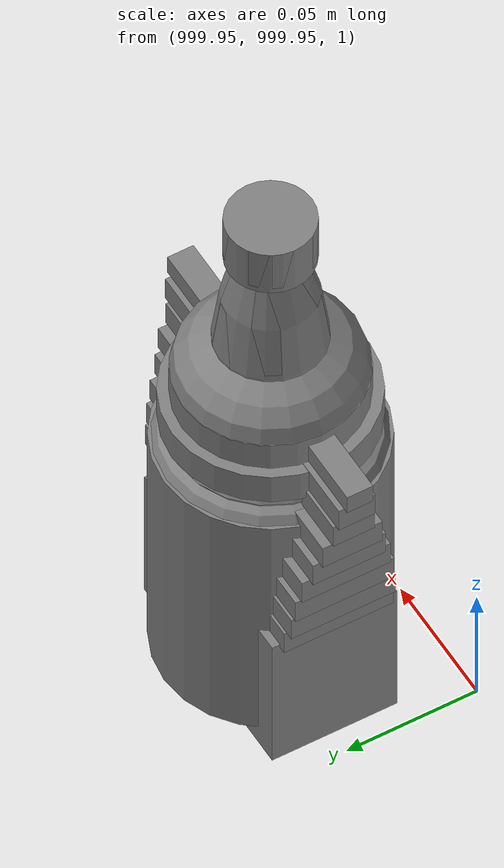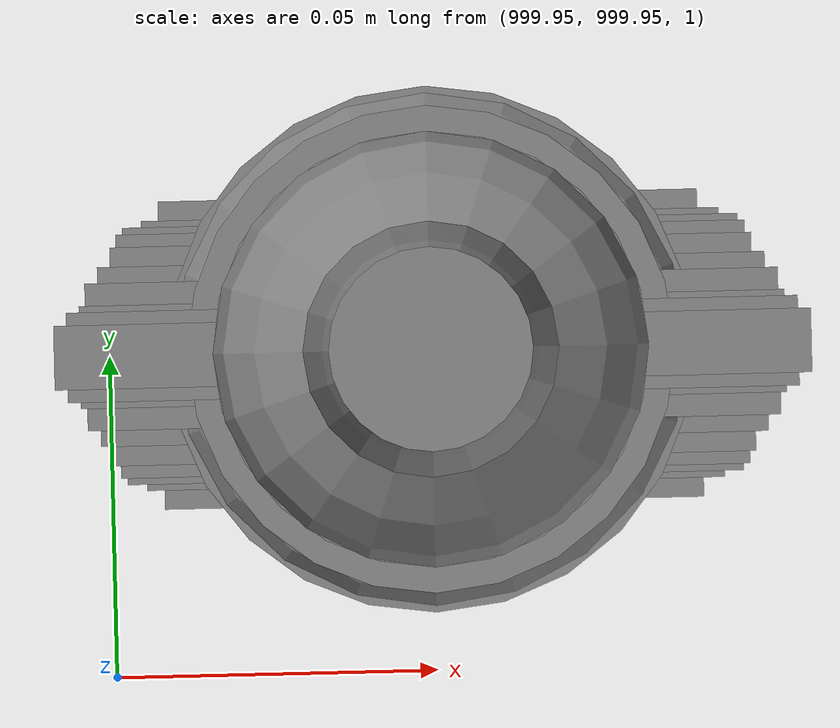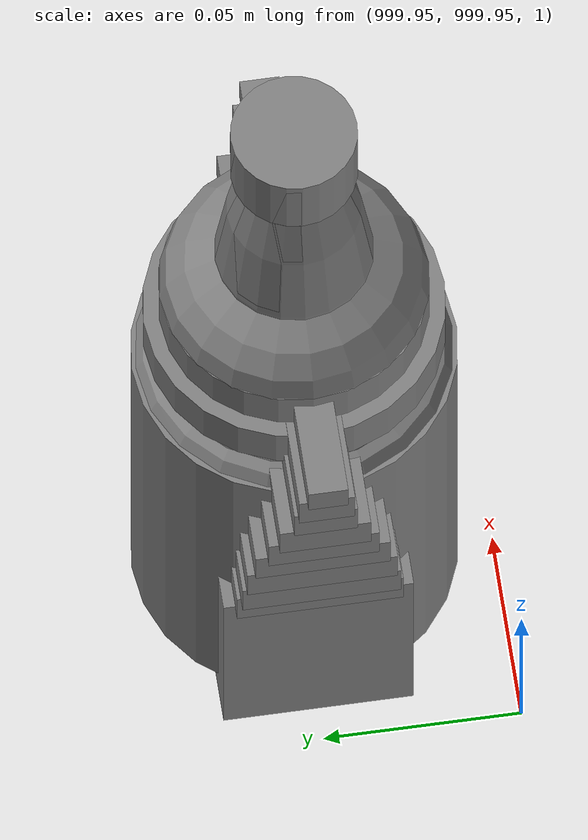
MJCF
<mujoco>
    <option gravity="0.000000000 0.000000000 -9.810000420" timestep="0.0166666" integrator="implicitfast" density="1.225" viscosity="1.8000001e-05" noslip_iterations="10" iterations="100" sdf_iterations="50">
        <flag multiccd="disable"/>
    </option>
    <size memory="1000M"/>
    <compiler coordinate="local"/>
    <worldbody>
        <light cutoff="30" pos="0 1 1" dir="0 -1 -2"/>
        <light cutoff="30" pos="0 -1 1" dir="0 1 -2"/>
        <body pos="-7.168000221 2.823999882 1.227496982" euler="-0.283413976 0.056829724 -0.133293271" name="openloong_gripper_2f85_fix_base_usda_Pos">
            <geom contype="1" conaffinity="1" density="1000" type="box" material="" rgba="0.500000000 0.500000000 0.500000000 1.000000000" solimp="0.899999976 0.949999988 0.001000000" friction="1.000000000 0.005000000 0.000100000" solref="0.020000000 1.000000000" margin="0" condim="3" group="0" pos="-0.002278805 0.074524641 -0.004134059" quat="0.315989345 0.948763072 -0.000000000 0.000000000" size="0.059999999 0.013000000 0.035000000" name="openloong_gripper_2f85_fix_base_usda_geom_EBFA9838_0139_4482_8962_D51A3C226F40"/>
            <geom contype="1" conaffinity="1" density="1000" type="box" material="" rgba="0.500000000 0.500000000 0.500000000 1.000000000" solimp="0.899999976 0.949999988 0.001000000" friction="1.000000000 0.005000000 0.000100000" solref="0.020000000 1.000000000" margin="0" condim="3" group="0" pos="-0.002278805 0.078031301 0.008128285" quat="0.990447521 -0.137893379 -0.000000000 -0.000000000" size="0.059999999 0.010000000 0.035000000" name="openloong_gripper_2f85_fix_base_usda_geom_7A491561_07CA_46ED_BFE7_CDBD018D919C"/>
            <geom contype="1" conaffinity="1" density="1000" type="box" material="" rgba="0.500000000 0.500000000 0.500000000 1.000000000" solimp="0.899999976 0.949999988 0.001000000" friction="1.000000000 0.005000000 0.000100000" solref="0.020000000 1.000000000" margin="0" condim="3" group="0" pos="-0.002278805 0.080785275 -0.002596974" quat="0.287325472 -0.957833409 0.000000000 -0.000000000" size="0.059999999 0.013000000 0.035000000" name="openloong_gripper_2f85_fix_base_usda_geom_24D589A8_433B_4129_A69F_78BD36C2AFB4"/>
            <geom contype="1" conaffinity="1" density="1000" type="box" material="" rgba="0.500000000 0.500000000 0.500000000 1.000000000" solimp="0.899999976 0.949999988 0.001000000" friction="1.000000000 0.005000000 0.000100000" solref="0.020000000 1.000000000" margin="0" condim="3" group="0" pos="-0.002278805 -0.098804474 -0.020146966" quat="0.988851666 0.148906454 0.000000000 -0.000000000" size="0.059999999 0.022000000 0.020000000" name="openloong_gripper_2f85_fix_base_usda_geom_04DFAF8B_A6BE_48C4_8EE0_F0E3441D2D47"/>
            <geom contype="1" conaffinity="1" density="1000" type="box" material="" rgba="0.500000000 0.500000000 0.500000000 1.000000000" solimp="0.899999976 0.949999988 0.001000000" friction="1.000000000 0.005000000 0.000100000" solref="0.020000000 1.000000000" margin="0" condim="3" group="0" pos="-0.002279282 0.019920111 0.012102962" quat="0.995421767 0.095583342 -0.000000000 -0.000000000" size="0.059999999 0.025000000 0.026000001" name="openloong_gripper_2f85_fix_base_usda_geom_C9FB6700_6BCE_4855_9438_82DE11560926"/>
            <geom contype="1" conaffinity="1" density="1000" type="box" material="" rgba="0.500000000 0.500000000 0.500000000 1.000000000" solimp="0.899999976 0.949999988 0.001000000" friction="1.000000000 0.005000000 0.000100000" solref="0.020000000 1.000000000" margin="0" condim="3" group="0" pos="-0.002279282 0.005734444 -0.014276862" quat="0.999571741 -0.029275302 -0.000000000 -0.000000000" size="0.059999999 0.050000001 0.010000000" name="openloong_gripper_2f85_fix_base_usda_geom_1181830C_35AE_4B8D_BE04_E9144BBB9F48"/>
            <geom contype="1" conaffinity="1" density="1000" type="box" material="" rgba="0.500000000 0.500000000 0.500000000 1.000000000" solimp="0.899999976 0.949999988 0.001000000" friction="1.000000000 0.005000000 0.000100000" solref="0.020000000 1.000000000" margin="0" condim="3" group="0" pos="-0.002278805 0.079460382 0.007771969" quat="0.922590554 -0.385781586 0.000000000 -0.000000000" size="0.059999999 0.010000000 0.035000000" name="openloong_gripper_2f85_fix_base_usda_geom_2F75411C_1EFA_4764_B030_B2607CCDCAED"/>
            <geom contype="1" conaffinity="1" density="1000" type="box" material="" rgba="0.500000000 0.500000000 0.500000000 1.000000000" solimp="0.899999976 0.949999988 0.001000000" friction="1.000000000 0.005000000 0.000100000" solref="0.020000000 1.000000000" margin="0" condim="3" group="0" pos="-0.002279282 0.081384182 -0.001320124" quat="0.590483785 -0.807049930 0.000000000 -0.000000000" size="0.059999999 0.013000000 0.035000000" name="openloong_gripper_2f85_fix_base_usda_geom_29560ACC_0507_4951_BB59_633DB611D710"/>
            <geom contype="1" conaffinity="1" density="1000" type="box" material="" rgba="0.500000000 0.500000000 0.500000000 1.000000000" solimp="0.899999976 0.949999988 0.001000000" friction="1.000000000 0.005000000 0.000100000" solref="0.020000000 1.000000000" margin="0" condim="3" group="0" pos="-0.002278805 -0.059297800 -0.007972836" quat="0.988851666 0.148906454 0.000000000 -0.000000000" size="0.059999999 0.020000000 0.022000000" name="openloong_gripper_2f85_fix_base_usda_geom_8E4429CE_6C72_4C43_8975_EF05E16B8272"/>
            <geom contype="1" conaffinity="1" density="1000" type="box" material="" rgba="0.500000000 0.500000000 0.500000000 1.000000000" solimp="0.899999976 0.949999988 0.001000000" friction="1.000000000 0.005000000 0.000100000" solref="0.020000000 1.000000000" margin="0" condim="3" group="0" pos="-0.002278805 0.076618671 -0.004656792" quat="0.004634961 0.999989629 -0.000000000 0.000000000" size="0.059999999 0.013000000 0.035000000" name="openloong_gripper_2f85_fix_base_usda_geom_FEB53519_97D9_4673_9A7B_9503C873F263"/>
            <geom contype="1" conaffinity="1" density="1000" type="box" material="" rgba="0.500000000 0.500000000 0.500000000 1.000000000" solimp="0.899999976 0.949999988 0.001000000" friction="1.000000000 0.005000000 0.000100000" solref="0.020000000 1.000000000" margin="0" condim="3" group="0" pos="-0.002279282 -0.021952629 0.002960086" quat="0.991270423 0.131847665 -0.000000000 0.000000000" size="0.059999999 0.020000000 0.024000000" name="openloong_gripper_2f85_fix_base_usda_geom_8AFA0BF3_40AE_4D8C_862E_E08A9224DE56"/>
            <geom contype="1" conaffinity="1" density="1000" type="box" material="" rgba="0.500000000 0.500000000 0.500000000 1.000000000" solimp="0.899999976 0.949999988 0.001000000" friction="1.000000000 0.005000000 0.000100000" solref="0.020000000 1.000000000" margin="0" condim="3" group="0" pos="-0.002278805 0.081418991 0.002587914" quat="0.803492308 -0.595315695 0.000000000 -0.000000000" size="0.059999999 0.013000000 0.035000000" name="openloong_gripper_2f85_fix_base_usda_geom_ADAAF34A_86D6_4DF4_AB03_610D70D9D694"/>
            <geom contype="1" conaffinity="1" density="1000" type="box" material="" rgba="0.500000000 0.500000000 0.500000000 1.000000000" solimp="0.899999976 0.949999988 0.001000000" friction="1.000000000 0.005000000 0.000100000" solref="0.020000000 1.000000000" margin="0" condim="3" group="0" pos="-0.002278805 0.061115503 0.008545756" quat="0.999326169 0.036714450 0.000000000 -0.000000000" size="0.059999999 0.020000000 0.035000000" name="openloong_gripper_2f85_fix_base_usda_geom_04DBD9E4_4F07_4D02_8F04_B6E85C615C81"/>
            <freejoint name="openloong_gripper_2f85_fix_base_usda_pos_scan"/>
        </body>
        <body pos="-1.811557651 5.949813843 1.698159814" euler="-152.295684814 66.920547485 139.588485718" mocap="true" name="spotlight2_SpotLight"/>
        <body pos="1000.000000000 1000.000000000 1.000000000" euler="0.000000000 0.000000000 0.000000000" name="openloong_gripper_2f85_fix_base_usda_jar_01">
            <geom contype="1" conaffinity="1" density="1000" type="box" material="" rgba="0.500000000 0.500000000 0.500000000 1.000000000" solimp="0.899999976 0.949999988 0.001000000" friction="1.000000000 0.005000000 0.000100000" solref="0.020000000 1.000000000" margin="0" condim="3" group="0" pos="0.000000000 0.000000000 0.006158113" quat="1.000000000 0.000000000 0.000000000 0.000000000" size="0.020000000 0.020000000 0.005000000" name="openloong_gripper_2f85_fix_base_usda_geom_D9FEA424_443F_4B69_B4DB_CABD7B9A64F4"/>
            <geom contype="1" conaffinity="1" density="1000" type="cylinder" material="" rgba="0.500000000 0.500000000 0.500000000 1.000000000" solimp="0.899999976 0.949999988 0.001000000" friction="1.000000000 0.005000000 0.000100000" solref="0.020000000 1.000000000" margin="0" condim="3" group="0" pos="0.000000000 0.000000000 0.062744498" quat="1.000000000 0.000000000 0.000000000 0.000000000" size="0.041000001 0.052999999 1.000000000" name="openloong_gripper_2f85_fix_base_usda_geom_06018C2E_68C7_45D9_9EDF_A142CDF6F5F6"/>
            <geom contype="1" conaffinity="1" density="1000" type="ellipsoid" material="" rgba="0.500000000 0.500000000 0.500000000 1.000000000" solimp="0.899999976 0.949999988 0.001000000" friction="1.000000000 0.005000000 0.000100000" solref="0.020000000 1.000000000" margin="0" condim="3" group="0" pos="0.000000000 0.000000000 0.122252703" quat="1.000000000 0.000000000 0.000000000 0.000000000" size="0.035999998 0.035999998 0.010000000" name="openloong_gripper_2f85_fix_base_usda_geom_8B200AE0_8C98_423F_83F3_BFC7848A0DEF"/>
            <geom contype="1" conaffinity="1" density="1000" type="cylinder" material="" rgba="0.500000000 0.500000000 0.500000000 1.000000000" solimp="0.899999976 0.949999988 0.001000000" friction="1.000000000 0.005000000 0.000100000" solref="0.020000000 1.000000000" margin="0" condim="3" group="0" pos="0.000000000 0.000000000 0.015747190" quat="1.000000000 0.000000000 0.000000000 0.000000000" size="0.035000000 0.010000000 1.000000000" name="openloong_gripper_2f85_fix_base_usda_geom_2267C392_1225_43C6_AF75_0BFD4115241B"/>
            <geom contype="1" conaffinity="1" density="1000" type="ellipsoid" material="" rgba="0.500000000 0.500000000 0.500000000 1.000000000" solimp="0.899999976 0.949999988 0.001000000" friction="1.000000000 0.005000000 0.000100000" solref="0.020000000 1.000000000" margin="0" condim="3" group="0" pos="0.000000000 0.000000000 0.115815401" quat="1.000000000 0.000000000 0.000000000 0.000000000" size="0.039999999 0.039999999 0.010000000" name="openloong_gripper_2f85_fix_base_usda_geom_2A868DA3_7755_4F34_8200_88FDADC4FA84"/>
            <geom contype="1" conaffinity="1" density="1000" type="cylinder" material="" rgba="0.500000000 0.500000000 0.500000000 1.000000000" solimp="0.899999976 0.949999988 0.001000000" friction="1.000000000 0.005000000 0.000100000" solref="0.020000000 1.000000000" margin="0" condim="3" group="0" pos="0.000000000 0.000000000 0.133183479" quat="1.000000000 0.000000000 0.000000000 0.000000000" size="0.037999999 0.006500000 1.000000000" name="openloong_gripper_2f85_fix_base_usda_geom_6615CD72_FCD1_4DD6_AE37_4D2E0B549FBA"/>
            <freejoint name="openloong_gripper_2f85_fix_base_usda_jar_01_joint"/>
            <site size="0.005000000 0.005000000 0.005000000" rgba="0.500000000 0.500000000 0.500000000 1.000000000" pos="0.000000000 0.000000000 0.000000000" quat="1.000000000 0.000000000 0.000000000 0.000000000" group="0" type="sphere" name="openloong_gripper_2f85_fix_base_usda_jar_01site"/>
        </body>
        <body pos="1000.000000000 1000.000000000 1.000000000" euler="0.000000000 0.000000000 0.000000000" name="openloong_gripper_2f85_fix_base_usda_bottle_blue">
            <geom contype="1" conaffinity="1" density="1000" type="ellipsoid" material="" rgba="0.500000000 0.500000000 0.500000000 1.000000000" solimp="0.899999976 0.949999988 0.001000000" friction="1.000000000 0.005000000 0.000100000" solref="0.020000000 1.000000000" margin="0" condim="3" group="0" pos="0.000000000 0.000000000 0.118920922" quat="1.000000000 0.000000000 0.000000000 0.000000000" size="0.030999999 0.030999999 0.029999999" name="openloong_gripper_2f85_fix_base_usda_geom_E7C21DD0_E9D7_4623_89EE_CD85DB114045"/>
            <geom contype="1" conaffinity="1" density="1000" type="box" material="" rgba="0.500000000 0.500000000 0.500000000 1.000000000" solimp="0.899999976 0.949999988 0.001000000" friction="1.000000000 0.005000000 0.000100000" solref="0.020000000 1.000000000" margin="0" condim="3" group="0" pos="0.000000000 0.000000000 0.002164602" quat="1.000000000 0.000000000 0.000000000 0.000000000" size="0.020000000 0.020000000 0.003000000" name="openloong_gripper_2f85_fix_base_usda_geom_915BDFD4_0372_4866_B9CA_84A4535C18F6"/>
            <geom contype="1" conaffinity="1" density="1000" type="cylinder" material="" rgba="0.500000000 0.500000000 0.500000000 1.000000000" solimp="0.899999976 0.949999988 0.001000000" friction="1.000000000 0.005000000 0.000100000" solref="0.020000000 1.000000000" margin="0" condim="3" group="0" pos="0.000000000 -0.000366211 0.060859680" quat="1.000000000 0.000000000 0.000000000 0.000000000" size="0.030999999 0.057999998 1.000000000" name="openloong_gripper_2f85_fix_base_usda_geom_BA520EE1_F50C_4B4C_9314_7A57CC563897"/>
            <geom contype="1" conaffinity="1" density="1000" type="cylinder" material="" rgba="0.500000000 0.500000000 0.500000000 1.000000000" solimp="0.899999976 0.949999988 0.001000000" friction="1.000000000 0.005000000 0.000100000" solref="0.020000000 1.000000000" margin="0" condim="3" group="0" pos="0.000000000 0.000000000 0.220594406" quat="1.000000000 0.000000000 0.000000000 0.000000000" size="0.016000001 0.010000000 1.000000000" name="openloong_gripper_2f85_fix_base_usda_geom_B37BEF18_0805_4953_BC78_4CA45D9FA523"/>
            <geom contype="1" conaffinity="1" density="1000" type="ellipsoid" material="" rgba="0.500000000 0.500000000 0.500000000 1.000000000" solimp="0.899999976 0.949999988 0.001000000" friction="1.000000000 0.005000000 0.000100000" solref="0.020000000 1.000000000" margin="0" condim="3" group="0" pos="0.000000000 0.000000000 0.144259930" quat="1.000000000 0.000000000 0.000000000 0.000000000" size="0.021000000 0.021000000 0.079999998" name="openloong_gripper_2f85_fix_base_usda_geom_6C80951B_1236_466C_A3C4_FCA443C55C45"/>
            <freejoint name="openloong_gripper_2f85_fix_base_usda_bottle_blue_joint"/>
            <site size="0.005000000 0.005000000 0.005000000" rgba="0.500000000 0.500000000 0.500000000 1.000000000" pos="0.000000000 0.000000000 0.000000000" quat="0.999961913 0.008726535 0.000000000 0.000000000" group="0" type="sphere" name="openloong_gripper_2f85_fix_base_usda_bottle_bluesite"/>
        </body>
        <body pos="1000.000000000 1000.000000000 1.000000000" euler="0.000000000 0.000000000 0.000000000" name="openloong_gripper_2f85_fix_base_usda_bottle_red">
            <geom contype="1" conaffinity="1" density="1000" type="ellipsoid" material="" rgba="0.500000000 0.500000000 0.500000000 1.000000000" solimp="0.899999976 0.949999988 0.001000000" friction="1.000000000 0.005000000 0.000100000" solref="0.020000000 1.000000000" margin="0" condim="3" group="0" pos="0.000000000 0.000000000 0.144284487" quat="1.000000000 0.000000000 0.000000000 0.000000000" size="0.021000000 0.021000000 0.079999998" name="openloong_gripper_2f85_fix_base_usda_geom_813BE818_1852_4A78_AC28_8934FF2CC4AB"/>
            <geom contype="1" conaffinity="1" density="1000" type="cylinder" material="" rgba="0.500000000 0.500000000 0.500000000 1.000000000" solimp="0.899999976 0.949999988 0.001000000" friction="1.000000000 0.005000000 0.000100000" solref="0.020000000 1.000000000" margin="0" condim="3" group="0" pos="0.000000000 0.000000000 0.220618963" quat="1.000000000 0.000000000 0.000000000 0.000000000" size="0.016000001 0.010000000 1.000000000" name="openloong_gripper_2f85_fix_base_usda_geom_556059A3_9FED_4D37_A33F_71F9532E9BB4"/>
            <geom contype="1" conaffinity="1" density="1000" type="ellipsoid" material="" rgba="0.500000000 0.500000000 0.500000000 1.000000000" solimp="0.899999976 0.949999988 0.001000000" friction="1.000000000 0.005000000 0.000100000" solref="0.020000000 1.000000000" margin="0" condim="3" group="0" pos="0.000000000 0.000000000 0.118945479" quat="1.000000000 0.000000000 0.000000000 0.000000000" size="0.030999999 0.030999999 0.029999999" name="openloong_gripper_2f85_fix_base_usda_geom_E3A54A60_B80F_4D35_9B6B_B8405F2187D6"/>
            <geom contype="1" conaffinity="1" density="1000" type="box" material="" rgba="0.500000000 0.500000000 0.500000000 1.000000000" solimp="0.899999976 0.949999988 0.001000000" friction="1.000000000 0.005000000 0.000100000" solref="0.020000000 1.000000000" margin="0" condim="3" group="0" pos="0.000000000 0.000000000 0.002189159" quat="1.000000000 0.000000000 0.000000000 0.000000000" size="0.020000000 0.020000000 0.003000000" name="openloong_gripper_2f85_fix_base_usda_geom_F9ACAFF8_9611_4069_9AB3_F898B79644C2"/>
            <geom contype="1" conaffinity="1" density="1000" type="cylinder" material="" rgba="0.500000000 0.500000000 0.500000000 1.000000000" solimp="0.899999976 0.949999988 0.001000000" friction="1.000000000 0.005000000 0.000100000" solref="0.020000000 1.000000000" margin="0" condim="3" group="0" pos="0.000000000 -0.000366211 0.060884237" quat="1.000000000 0.000000000 0.000000000 0.000000000" size="0.030999999 0.057999998 1.000000000" name="openloong_gripper_2f85_fix_base_usda_geom_31E7BB88_D06F_4CC1_984D_6F3199016EAD"/>
            <freejoint name="openloong_gripper_2f85_fix_base_usda_bottle_red_joint"/>
            <site size="0.005000000 0.005000000 0.005000000" rgba="0.500000000 0.500000000 0.500000000 1.000000000" pos="0.000000000 0.000000000 0.000000000" quat="0.999961913 0.008726535 0.000000000 0.000000000" group="0" type="sphere" name="openloong_gripper_2f85_fix_base_usda_bottle_redsite"/>
        </body>
        <body pos="-1.991757035 5.789933681 1.684638023" euler="-59.725875854 -14.184586525 168.938217163" mocap="true" name="spotlight4_SpotLight"/>
        <body pos="1000.000000000 1000.000000000 1.000000000" euler="0.000000000 0.000000000 0.000000000" name="openloong_gripper_2f85_fix_base_usda_salt">
            <geom contype="1" conaffinity="1" density="1000" type="box" material="" rgba="0.500000000 0.500000000 0.500000000 1.000000000" solimp="0.899999976 0.949999988 0.001000000" friction="1.000000000 0.005000000 0.000100000" solref="0.020000000 1.000000000" margin="0" condim="3" group="0" pos="0.000305176 0.000000000 0.084862232" quat="1.000000000 0.000000000 0.000000000 0.000000000" size="0.048999999 0.018999999 0.005000000" name="openloong_gripper_2f85_fix_base_usda_geom_C41FAD3A_9A20_4848_BF2F_07C311860108"/>
            <geom contype="1" conaffinity="1" density="1000" type="box" material="" rgba="0.500000000 0.500000000 0.500000000 1.000000000" solimp="0.899999976 0.949999988 0.001000000" friction="1.000000000 0.005000000 0.000100000" solref="0.020000000 1.000000000" margin="0" condim="3" group="0" pos="0.000305176 0.000000000 0.104564309" quat="1.000000000 0.000000000 0.000000000 0.000000000" size="0.052000001 0.014000000 0.005000000" name="openloong_gripper_2f85_fix_base_usda_geom_78BE568E_0317_43F9_B308_E6C0E41BC143"/>
            <geom contype="1" conaffinity="1" density="1000" type="box" material="" rgba="0.500000000 0.500000000 0.500000000 1.000000000" solimp="0.899999976 0.949999988 0.001000000" friction="1.000000000 0.005000000 0.000100000" solref="0.020000000 1.000000000" margin="0" condim="3" group="0" pos="0.000305176 0.000000000 0.114487171" quat="1.000000000 0.000000000 0.000000000 0.000000000" size="0.054000001 0.011500000 0.005000000" name="openloong_gripper_2f85_fix_base_usda_geom_90FC012C_1717_4C63_A485_67575A2C74B2"/>
            <geom contype="1" conaffinity="1" density="1000" type="box" material="" rgba="0.500000000 0.500000000 0.500000000 1.000000000" solimp="0.899999976 0.949999988 0.001000000" friction="1.000000000 0.005000000 0.000100000" solref="0.020000000 1.000000000" margin="0" condim="3" group="0" pos="0.000305176 0.000000000 0.075103164" quat="1.000000000 0.000000000 0.000000000 0.000000000" size="0.048000000 0.020000000 0.005000000" name="openloong_gripper_2f85_fix_base_usda_geom_3F8877AD_E85B_45BE_BB12_56059EE3E887"/>
            <geom contype="1" conaffinity="1" density="1000" type="box" material="" rgba="0.500000000 0.500000000 0.500000000 1.000000000" solimp="0.899999976 0.949999988 0.001000000" friction="1.000000000 0.005000000 0.000100000" solref="0.020000000 1.000000000" margin="0" condim="3" group="0" pos="0.000305176 0.000000000 0.134892464" quat="1.000000000 0.000000000 0.000000000 0.000000000" size="0.057000000 0.007000000 0.005000000" name="openloong_gripper_2f85_fix_base_usda_geom_8E770E2F_6313_4CE9_B75A_05B0F29A7B95"/>
            <geom contype="1" conaffinity="1" density="1000" type="box" material="" rgba="0.500000000 0.500000000 0.500000000 1.000000000" solimp="0.899999976 0.949999988 0.001000000" friction="1.000000000 0.005000000 0.000100000" solref="0.020000000 1.000000000" margin="0" condim="3" group="0" pos="0.000305176 0.000000000 0.094920278" quat="1.000000000 0.000000000 0.000000000 0.000000000" size="0.050000001 0.017000001 0.005000000" name="openloong_gripper_2f85_fix_base_usda_geom_A8A808EB_67F1_4DDD_A52C_2CFFDA998646"/>
            <geom contype="1" conaffinity="1" density="1000" type="box" material="" rgba="0.500000000 0.500000000 0.500000000 1.000000000" solimp="0.899999976 0.949999988 0.001000000" friction="1.000000000 0.005000000 0.000100000" solref="0.020000000 1.000000000" margin="0" condim="3" group="0" pos="0.000305176 0.000000000 0.065204859" quat="1.000000000 0.000000000 0.000000000 0.000000000" size="0.045000002 0.021000000 0.005000000" name="openloong_gripper_2f85_fix_base_usda_geom_5458FF71_517B_4292_84DD_972F1ED61610"/>
            <geom contype="1" conaffinity="1" density="1000" type="box" material="" rgba="0.500000000 0.500000000 0.500000000 1.000000000" solimp="0.899999976 0.949999988 0.001000000" friction="1.000000000 0.005000000 0.000100000" solref="0.020000000 1.000000000" margin="0" condim="3" group="0" pos="0.000305176 0.000000000 0.144135714" quat="1.000000000 0.000000000 0.000000000 0.000000000" size="0.059000000 0.005000000 0.004000000" name="openloong_gripper_2f85_fix_base_usda_geom_205FA64F_67CA_4B78_A724_CDA523F554E9"/>
            <geom contype="1" conaffinity="1" density="1000" type="box" material="" rgba="0.500000000 0.500000000 0.500000000 1.000000000" solimp="0.899999976 0.949999988 0.001000000" friction="1.000000000 0.005000000 0.000100000" solref="0.020000000 1.000000000" margin="0" condim="3" group="0" pos="0.000000000 0.000000000 0.031593561" quat="1.000000000 0.000000000 0.000000000 0.000000000" size="0.041999999 0.024000000 0.029999999" name="openloong_gripper_2f85_fix_base_usda_geom_4F36B5F4_5C49_4FF9_BE3A_9CCAEFB632C7"/>
            <geom contype="1" conaffinity="1" density="1000" type="box" material="" rgba="0.500000000 0.500000000 0.500000000 1.000000000" solimp="0.899999976 0.949999988 0.001000000" friction="1.000000000 0.005000000 0.000100000" solref="0.020000000 1.000000000" margin="0" condim="3" group="0" pos="0.000305176 0.000000000 0.124608755" quat="1.000000000 0.000000000 0.000000000 0.000000000" size="0.055000000 0.008000000 0.005000000" name="openloong_gripper_2f85_fix_base_usda_geom_8D1BD7F5_5742_4A13_AF76_87BA46191555"/>
            <freejoint name="openloong_gripper_2f85_fix_base_usda_salt_joint"/>
            <site size="0.005000000 0.005000000 0.005000000" rgba="0.500000000 0.500000000 0.500000000 1.000000000" pos="0.000000000 0.000000000 0.000000000" quat="1.000000000 0.000000000 0.000000000 0.000000000" group="0" type="sphere" name="openloong_gripper_2f85_fix_base_usda_saltsite"/>
        </body>
        <body pos="1000.000000000 1000.000000000 1.000000000" euler="0.000000000 0.000000000 0.000000000" name="openloong_gripper_2f85_fix_base_usda_can">
            <geom contype="1" conaffinity="1" density="1000" type="cylinder" material="" rgba="0.500000000 0.500000000 0.500000000 1.000000000" solimp="0.899999976 0.949999988 0.001000000" friction="1.000000000 0.005000000 0.000100000" solref="0.020000000 1.000000000" margin="0" condim="3" group="0" pos="0.000000000 0.000000000 0.079676986" quat="1.000000000 0.000000000 0.000000000 0.000000000" size="0.034000002 0.071999997 1.000000000" name="openloong_gripper_2f85_fix_base_usda_geom_27EF3728_4990_427D_863C_84D039F04C2D"/>
            <geom contype="1" conaffinity="1" density="1000" type="ellipsoid" material="" rgba="0.500000000 0.500000000 0.500000000 1.000000000" solimp="0.899999976 0.949999988 0.001000000" friction="1.000000000 0.005000000 0.000100000" solref="0.020000000 1.000000000" margin="0" condim="3" group="0" pos="0.000000000 0.000000000 0.151854277" quat="1.000000000 0.000000000 0.000000000 0.000000000" size="0.034000002 0.034000002 0.020000000" name="openloong_gripper_2f85_fix_base_usda_geom_68828AA1_B96F_4666_99C6_44846355F99B"/>
            <geom contype="1" conaffinity="1" density="1000" type="box" material="" rgba="0.500000000 0.500000000 0.500000000 1.000000000" solimp="0.899999976 0.949999988 0.001000000" friction="1.000000000 0.005000000 0.000100000" solref="0.020000000 1.000000000" margin="0" condim="3" group="0" pos="0.000000000 0.000000000 0.004777670" quat="1.000000000 0.000000000 0.000000000 0.000000000" size="0.020000000 0.020000000 0.005000000" name="openloong_gripper_2f85_fix_base_usda_geom_D61C8DC6_C299_4336_B264_111F4A7C3CD2"/>
            <freejoint name="openloong_gripper_2f85_fix_base_usda_can_joint"/>
            <site size="0.005000000 0.005000000 0.005000000" rgba="0.500000000 0.500000000 0.500000000 1.000000000" pos="0.000000000 0.000000000 0.000000000" quat="1.000000000 0.000000000 0.000000000 0.000000000" group="0" type="sphere" name="openloong_gripper_2f85_fix_base_usda_cansite"/>
        </body>
        <body pos="-2.187613249 5.962965965 1.848310709" euler="140.798721313 55.850997925 -148.912704468" mocap="true" name="spotlight3_SpotLight"/>
        <body pos="0.000000000 0.000000000 0.000000000" euler="0.000000000 0.000000000 0.000000000" name="Interactive Objects_Interactive Objects"/>
        <body pos="0.000000000 0.000000000 0.000000000" euler="0.000000000 0.000000000 0.000000000" name=" Static Objects_ Static Objects">
            <geom contype="1" conaffinity="1" density="1000" type="box" material="" rgba="0.500000000 0.500000000 0.500000000 1.000000000" solimp="0.899999976 0.949999988 0.001000000" friction="1.000000000 0.005000000 0.000100000" solref="0.020000000 1.000000000" margin="0" condim="3" group="0" pos="-6.286010742 6.153595448 1.563861728" quat="0.707107067 0.000000000 0.000000000 0.707106471" size="0.529999971 3.134999990 0.025000000" name=" Static Objects_geom_14171B55_2791_42A6_B688_70BB21FA4E3B"/>
            <geom contype="1" conaffinity="1" density="1000" type="box" material="" rgba="0.500000000 0.500000000 0.500000000 1.000000000" solimp="0.899999976 0.949999988 0.001000000" friction="1.000000000 0.005000000 0.000100000" solref="0.020000000 1.000000000" margin="0" condim="3" group="0" pos="-3.101639986 6.150595188 1.018643856" quat="1.000000000 0.000000000 0.000000000 0.000000000" size="0.050000001 0.579999983 1.019999981" name=" Static Objects_geom_DFDF6774_0090_4791_BDE9_9BC603D9A30E"/>
            <geom contype="1" conaffinity="1" density="1000" type="box" material="" rgba="0.500000000 0.500000000 0.500000000 1.000000000" solimp="0.899999976 0.949999988 0.001000000" friction="1.000000000 0.005000000 0.000100000" solref="0.020000000 1.000000000" margin="0" condim="3" group="0" pos="-2.825197220 6.153595448 1.563861728" quat="0.707107067 0.000000000 0.000000000 0.707106471" size="0.550000012 0.239999995 0.025000000" name=" Static Objects_geom_3EB43B2B_A087_4430_8C15_8E2F58B70B50"/>
            <geom contype="1" conaffinity="1" density="1000" type="box" material="" rgba="0.500000000 0.500000000 0.500000000 1.000000000" solimp="0.899999976 0.949999988 0.001000000" friction="1.000000000 0.005000000 0.000100000" solref="0.020000000 1.000000000" margin="0" condim="3" group="0" pos="-6.311686516 6.153595448 1.018643856" quat="0.707107067 0.000000000 0.000000000 0.707106471" size="0.050000001 3.150000095 1.019999981" name=" Static Objects_geom_1667C201_7562_4ED1_BA4C_38AC2EB849D8"/>
            <geom contype="1" conaffinity="1" density="1000" type="box" material="" rgba="0.500000000 0.500000000 0.500000000 1.000000000" solimp="0.899999976 0.949999988 0.001000000" friction="1.000000000 0.005000000 0.000100000" solref="0.020000000 1.000000000" margin="0" condim="3" group="0" pos="-2.825197220 6.153595448 1.115278244" quat="0.707107067 0.000000000 0.000000000 0.707106471" size="0.550000012 0.239999995 0.025000000" name=" Static Objects_geom_91D057F3_5A09_44B5_82B3_F4833A7F5544"/>
            <geom contype="1" conaffinity="1" density="1000" type="box" material="" rgba="0.500000000 0.500000000 0.500000000 1.000000000" solimp="0.899999976 0.949999988 0.001000000" friction="1.000000000 0.005000000 0.000100000" solref="0.020000000 1.000000000" margin="0" condim="3" group="0" pos="-6.293097973 6.153595448 1.114443064" quat="0.707107067 0.000000000 0.000000000 0.707106471" size="0.529999971 3.134999990 0.025000000" name=" Static Objects_geom_6039CDED_4588_451A_8CFE_138348427E76"/>
            <geom contype="1" conaffinity="1" density="1000" type="box" material="" rgba="0.500000000 0.500000000 0.500000000 1.000000000" solimp="0.899999976 0.949999988 0.001000000" friction="1.000000000 0.005000000 0.000100000" solref="0.020000000 1.000000000" margin="0" condim="3" group="0" pos="-2.825197220 6.153595448 0.629031777" quat="0.707107067 0.000000000 0.000000000 0.707106471" size="0.550000012 0.239999995 0.025000000" name=" Static Objects_geom_C4649103_799F_4B2F_B570_E913E4742128"/>
            <geom contype="1" conaffinity="1" density="1000" type="box" material="" rgba="0.500000000 0.500000000 0.500000000 1.000000000" solimp="0.899999976 0.949999988 0.001000000" friction="1.000000000 0.005000000 0.000100000" solref="0.020000000 1.000000000" margin="0" condim="3" group="0" pos="-6.286010742 6.153595448 0.096129179" quat="0.707107067 0.000000000 0.000000000 0.707106471" size="0.529999971 3.134999990 0.098999999" name=" Static Objects_geom_AC5CE194_F16D_4F4A_855E_F119AEC67846"/>
            <geom contype="1" conaffinity="1" density="1000" type="box" material="" rgba="0.500000000 0.500000000 0.500000000 1.000000000" solimp="0.899999976 0.949999988 0.001000000" friction="1.000000000 0.005000000 0.000100000" solref="0.020000000 1.000000000" margin="0" condim="3" group="0" pos="-2.825197220 6.153595448 0.097434282" quat="0.707107067 0.000000000 0.000000000 0.707106471" size="0.550000012 0.239999995 0.098999999" name=" Static Objects_geom_15E22479_8C4C_4243_A558_ADC1C86B64A2"/>
            <geom contype="1" conaffinity="1" density="1000" type="box" material="" rgba="0.500000000 0.500000000 0.500000000 1.000000000" solimp="0.899999976 0.949999988 0.001000000" friction="1.000000000 0.005000000 0.000100000" solref="0.020000000 1.000000000" margin="0" condim="3" group="0" pos="-6.286010742 6.153595448 0.629031777" quat="0.707107067 0.000000000 0.000000000 0.707106471" size="0.529999971 3.134999990 0.025000000" name=" Static Objects_geom_C7150609_15E3_4C10_9EB6_9FE9CF8C80CF"/>
            <geom contype="1" conaffinity="1" density="1000" type="box" material="" rgba="0.500000000 0.500000000 0.500000000 1.000000000" solimp="0.899999976 0.949999988 0.001000000" friction="1.000000000 0.005000000 0.000100000" solref="0.020000000 1.000000000" margin="0" condim="3" group="0" pos="-6.000000000 20.159999847 2.000000000" quat="1.000000000 0.000000000 0.000000000 0.000000000" size="6.079999924 0.070000000 2.000000000" name=" Static Objects_geom_BDDB03D3_8AC2_4F71_BF64_100A1682DE0C"/>
            <geom contype="1" conaffinity="1" density="1000" type="box" material="" rgba="0.500000000 0.500000000 0.500000000 1.000000000" solimp="0.899999976 0.949999988 0.001000000" friction="1.000000000 0.005000000 0.000100000" solref="0.020000000 1.000000000" margin="0" condim="3" group="0" pos="-6.000000000 0.035000000 2.000000000" quat="1.000000000 0.000000000 0.000000000 0.000000000" size="6.079999924 0.070000000 2.000000000" name=" Static Objects_geom_29435641_8F5D_4324_80BB_B35442520214"/>
            <geom contype="1" conaffinity="1" density="1000" type="box" material="" rgba="0.500000000 0.500000000 0.500000000 1.000000000" solimp="0.899999976 0.949999988 0.001000000" friction="1.000000000 0.005000000 0.000100000" solref="0.020000000 1.000000000" margin="0" condim="3" group="0" pos="0.000000000 10.000000000 2.000000000" quat="1.000000000 0.000000000 0.000000000 0.000000000" size="0.070000000 10.500000000 2.000000000" name=" Static Objects_geom_0FD932E0_B91A_4AB4_AB5B_1198F9AA2C94"/>
            <geom contype="1" conaffinity="1" density="1000" type="box" material="" rgba="0.500000000 0.500000000 0.500000000 1.000000000" solimp="0.899999976 0.949999988 0.001000000" friction="1.000000000 0.005000000 0.000100000" solref="0.020000000 1.000000000" margin="0" condim="3" group="0" pos="-12.050000191 10.000000000 2.000000000" quat="1.000000000 0.000000000 0.000000000 0.000000000" size="0.070000000 10.500000000 2.000000000" name=" Static Objects_geom_B0DE543F_5FDA_4C32_B881_2754B42AF7B7"/>
            <geom contype="1" conaffinity="1" density="1000" type="plane" material="" rgba="0.500000000 0.500000000 0.500000000 1.000000000" solimp="0.899999976 0.949999988 0.001000000" friction="1.000000000 0.005000000 0.000100000" solref="0.020000000 1.000000000" margin="0" condim="3" group="0" pos="-6.000000000 10.399999619 0.000000000" quat="1.000000000 0.000000000 0.000000000 0.000000000" size="6.050000191 10.800000191 0.010000000" name=" Static Objects_geom_54558FE0_F25C_4BF5_8446_35A251ACC755"/>
            <geom contype="1" conaffinity="1" density="1000" type="box" material="" rgba="0.500000000 0.500000000 0.500000000 1.000000000" solimp="0.899999976 0.949999988 0.001000000" friction="1.000000000 0.005000000 0.000100000" solref="0.020000000 1.000000000" margin="0" condim="3" group="0" pos="-8.830721855 2.096410990 0.549305558" quat="1.000000000 0.000000000 0.000000000 0.000000000" size="0.280000001 0.430000007 0.550000012" name=" Static Objects_geom_2E0E5990_BDF5_4B37_8134_9EB7973D5297"/>
            <geom contype="1" conaffinity="1" density="1000" type="box" material="" rgba="0.500000000 0.500000000 0.500000000 1.000000000" solimp="0.899999976 0.949999988 0.001000000" friction="1.000000000 0.005000000 0.000100000" solref="0.020000000 1.000000000" margin="0" condim="3" group="0" pos="-6.460197449 2.937205315 0.548931718" quat="1.000000000 0.000000000 0.000000000 0.000000000" size="2.650000095 0.430000007 0.550000012" name=" Static Objects_geom_C628ADC5_393B_4863_AB8F_4E924F6F439C"/>
            <geom contype="1" conaffinity="1" density="1000" type="box" material="" rgba="0.500000000 0.500000000 0.500000000 1.000000000" solimp="0.899999976 0.949999988 0.001000000" friction="1.000000000 0.005000000 0.000100000" solref="0.020000000 1.000000000" margin="0" condim="3" group="0" pos="-4.240264893 1.327049494 0.549888909" quat="1.000000000 0.000000000 0.000000000 0.000000000" size="0.430000007 1.200000048 0.550000012" name=" Static Objects_geom_0BD0CD77_58DD_4CD7_B166_BD81F8DD41B2"/>
            <geom contype="1" conaffinity="1" density="1000" type="box" material="" rgba="0.500000000 0.500000000 0.500000000 1.000000000" solimp="0.899999976 0.949999988 0.001000000" friction="1.000000000 0.005000000 0.000100000" solref="0.020000000 1.000000000" margin="0" condim="3" group="0" pos="-7.408766270 3.088089943 1.776644945" quat="0.928051054 0.000000000 0.000000000 0.372453064" size="0.050000001 0.100000001 0.050000001" name=" Static Objects_geom_9C816A10_6552_4BCF_95B0_94F4DAFDE6E0"/>
            <geom contype="1" conaffinity="1" density="1000" type="box" material="" rgba="0.500000000 0.500000000 0.500000000 1.000000000" solimp="0.899999976 0.949999988 0.001000000" friction="1.000000000 0.005000000 0.000100000" solref="0.020000000 1.000000000" margin="0" condim="3" group="0" pos="-7.437745571 3.067511320 1.289965630" quat="1.000000000 0.000000000 0.000000000 0.000000000" size="0.029999999 0.020000000 0.020000000" name=" Static Objects_geom_F25A9C99_519A_48EE_9FD7_57639B068AE2"/>
            <geom contype="1" conaffinity="1" density="1000" type="box" material="" rgba="0.500000000 0.500000000 0.500000000 1.000000000" solimp="0.899999976 0.949999988 0.001000000" friction="1.000000000 0.005000000 0.000100000" solref="0.020000000 1.000000000" margin="0" condim="3" group="0" pos="-7.719123363 2.867671013 1.173410416" quat="1.000000000 0.000000000 0.000000000 0.000000000" size="0.250000000 0.250000000 0.079999998" name=" Static Objects_geom_DF3E29D4_EC89_4459_AF4D_E98A256119DD"/>
            <geom contype="1" conaffinity="1" density="1000" type="box" material="" rgba="0.500000000 0.500000000 0.500000000 1.000000000" solimp="0.899999976 0.949999988 0.001000000" friction="1.000000000 0.005000000 0.000100000" solref="0.020000000 1.000000000" margin="0" condim="3" group="0" pos="-7.719123363 2.958004713 1.530241251" quat="1.000000000 0.000000000 0.000000000 0.000000000" size="0.250000000 0.159999996 0.280000001" name=" Static Objects_geom_F2DE92EC_138B_46B7_A149_2FA6D0634BF3"/>
            <geom contype="1" conaffinity="1" density="1000" type="cylinder" material="" rgba="0.500000000 0.500000000 0.500000000 1.000000000" solimp="0.899999976 0.949999988 0.001000000" friction="1.000000000 0.005000000 0.000100000" solref="0.020000000 1.000000000" margin="0" condim="3" group="0" pos="-7.427312374 3.069516420 1.502544641" quat="0.928051054 0.000000000 0.000000000 0.372453064" size="0.015000000 0.230000004 0.100000001" name=" Static Objects_geom_D051A517_A7DE_4210_A8D9_AD2C6780E3C6"/>
            <geom contype="1" conaffinity="1" density="1000" type="box" material="" rgba="0.500000000 0.500000000 0.500000000 1.000000000" solimp="0.899999976 0.949999988 0.001000000" friction="1.000000000 0.005000000 0.000100000" solref="0.020000000 1.000000000" margin="0" condim="3" group="0" pos="-9.058088303 6.434794426 1.209077358" quat="1.000000000 0.000000000 0.000000000 0.000000000" size="0.250000000 0.100000001 0.070000000" name=" Static Objects_geom_7E3C06FB_9264_4612_8136_9C66228F4B10"/>
            <geom contype="1" conaffinity="1" density="1000" type="box" material="" rgba="0.500000000 0.500000000 0.500000000 1.000000000" solimp="0.899999976 0.949999988 0.001000000" friction="1.000000000 0.005000000 0.000100000" solref="0.020000000 1.000000000" margin="0" condim="3" group="0" pos="-5.611940861 6.318420410 0.350975692" quat="1.000000000 0.000000000 0.000000000 0.000000000" size="0.699999988 0.100000001 0.150000006" name=" Static Objects_geom_7C387ED2_DA3C_4063_9839_1D4092539EC5"/>
            <geom contype="1" conaffinity="1" density="1000" type="box" material="" rgba="0.500000000 0.500000000 0.500000000 1.000000000" solimp="0.899999976 0.949999988 0.001000000" friction="1.000000000 0.005000000 0.000100000" solref="0.020000000 1.000000000" margin="0" condim="3" group="0" pos="-9.237723351 6.464855671 1.209077358" quat="1.000000000 0.000000000 0.000000000 0.000000000" size="0.100000001 0.100000001 0.070000000" name=" Static Objects_geom_323BEA9D_EF8A_4BE7_A4C9_DCD3E1A20623"/>
            <geom contype="1" conaffinity="1" density="1000" type="box" material="" rgba="0.500000000 0.500000000 0.500000000 1.000000000" solimp="0.899999976 0.949999988 0.001000000" friction="1.000000000 0.005000000 0.000100000" solref="0.020000000 1.000000000" margin="0" condim="3" group="0" pos="-6.300771236 6.459744930 1.744376063" quat="1.000000000 0.000000000 0.000000000 0.000000000" size="3.000000000 0.200000003 0.150000006" name=" Static Objects_geom_AEFE9FE9_2496_4265_9B61_FFE203CB1A78"/>
            <geom contype="1" conaffinity="1" density="1000" type="box" material="" rgba="0.500000000 0.500000000 0.500000000 1.000000000" solimp="0.899999976 0.949999988 0.001000000" friction="1.000000000 0.005000000 0.000100000" solref="0.020000000 1.000000000" margin="0" condim="3" group="0" pos="-7.373087406 6.458900928 1.214329123" quat="1.000000000 0.000000000 0.000000000 0.000000000" size="0.250000000 0.200000003 0.075000003" name=" Static Objects_geom_0216FBDC_D70B_4A80_AD7C_483FF2ADF072"/>
            <geom contype="1" conaffinity="1" density="1000" type="box" material="" rgba="0.500000000 0.500000000 0.500000000 1.000000000" solimp="0.899999976 0.949999988 0.001000000" friction="1.000000000 0.005000000 0.000100000" solref="0.020000000 1.000000000" margin="0" condim="3" group="0" pos="-4.035642624 6.459744930 0.352518857" quat="1.000000000 0.000000000 0.000000000 0.000000000" size="0.800000012 0.200000003 0.150000006" name=" Static Objects_geom_1877CFF2_A56C_4956_BF3E_77AF27441415"/>
            <geom contype="1" conaffinity="1" density="1000" type="box" material="" rgba="0.500000000 0.500000000 0.500000000 1.000000000" solimp="0.899999976 0.949999988 0.001000000" friction="1.000000000 0.005000000 0.000100000" solref="0.020000000 1.000000000" margin="0" condim="3" group="0" pos="-3.907610416 6.318625927 0.800981164" quat="1.000000000 0.000000000 0.000000000 0.000000000" size="0.500000000 0.100000001 0.150000006" name=" Static Objects_geom_49BA2B25_1803_4EDB_B2F7_D135C8DC9BCB"/>
            <geom contype="1" conaffinity="1" density="1000" type="box" material="" rgba="0.500000000 0.500000000 0.500000000 1.000000000" solimp="0.899999976 0.949999988 0.001000000" friction="1.000000000 0.005000000 0.000100000" solref="0.020000000 1.000000000" margin="0" condim="3" group="0" pos="-6.098561764 6.327973843 1.292199373" quat="1.000000000 0.000000000 0.000000000 0.000000000" size="0.500000000 0.100000001 0.150000006" name=" Static Objects_geom_2DCBD087_2669_4D69_94D3_8B77E7665FB5"/>
            <geom contype="1" conaffinity="1" density="1000" type="box" material="" rgba="0.500000000 0.500000000 0.500000000 1.000000000" solimp="0.899999976 0.949999988 0.001000000" friction="1.000000000 0.005000000 0.000100000" solref="0.020000000 1.000000000" margin="0" condim="3" group="0" pos="-7.886891365 6.459744930 0.352518857" quat="1.000000000 0.000000000 0.000000000 0.000000000" size="1.500000000 0.200000003 0.150000006" name=" Static Objects_geom_197FA620_FCDE_4874_96DE_2D7AAE56B1EC"/>
            <geom contype="1" conaffinity="1" density="1000" type="box" material="" rgba="0.500000000 0.500000000 0.500000000 1.000000000" solimp="0.899999976 0.949999988 0.001000000" friction="1.000000000 0.005000000 0.000100000" solref="0.020000000 1.000000000" margin="0" condim="3" group="0" pos="-6.824534416 6.447464466 1.212718010" quat="1.000000000 0.000000000 0.000000000 0.000000000" size="0.100000001 0.100000001 0.075000003" name=" Static Objects_geom_01FB794A_9145_40B2_BF0E_13A965CC3357"/>
            <geom contype="1" conaffinity="1" density="1000" type="box" material="" rgba="0.500000000 0.500000000 0.500000000 1.000000000" solimp="0.899999976 0.949999988 0.001000000" friction="1.000000000 0.005000000 0.000100000" solref="0.020000000 1.000000000" margin="0" condim="3" group="0" pos="-4.407354832 6.459744930 1.292199373" quat="1.000000000 0.000000000 0.000000000 0.000000000" size="1.240000010 0.200000003 0.150000006" name=" Static Objects_geom_CC4E0269_1D99_4175_964F_A91142131A46"/>
            <geom contype="1" conaffinity="1" density="1000" type="box" material="" rgba="0.500000000 0.500000000 0.500000000 1.000000000" solimp="0.899999976 0.949999988 0.001000000" friction="1.000000000 0.005000000 0.000100000" solref="0.020000000 1.000000000" margin="0" condim="3" group="0" pos="-6.751636982 6.459744930 0.800981164" quat="1.000000000 0.000000000 0.000000000 0.000000000" size="2.200000048 0.200000003 0.150000006" name=" Static Objects_geom_650F2DB9_EBE5_4B0B_8E62_CBC6212E5197"/>
            <geom contype="1" conaffinity="1" density="1000" type="box" material="" rgba="0.500000000 0.500000000 0.500000000 1.000000000" solimp="0.899999976 0.949999988 0.001000000" friction="1.000000000 0.005000000 0.000100000" solref="0.020000000 1.000000000" margin="0" condim="3" group="0" pos="-6.924745083 6.362090111 1.214329123" quat="1.000000000 0.000000000 0.000000000 0.000000000" size="0.200000003 0.100000001 0.075000003" name=" Static Objects_geom_0ED13F82_041D_4E23_B4CD_FEB383596124"/>
            <geom contype="1" conaffinity="1" density="1000" type="box" material="" rgba="0.500000000 0.500000000 0.500000000 1.000000000" solimp="0.899999976 0.949999988 0.001000000" friction="1.000000000 0.005000000 0.000100000" solref="0.020000000 1.000000000" margin="0" condim="3" group="0" pos="-8.844120979 6.464855671 1.209077358" quat="1.000000000 0.000000000 0.000000000 0.000000000" size="0.100000001 0.100000001 0.070000000" name=" Static Objects_geom_482B96F2_20B4_45C1_B2B7_CFA90FA44535"/>
            <geom contype="1" conaffinity="1" density="1000" type="box" material="" rgba="0.500000000 0.500000000 0.500000000 1.000000000" solimp="0.899999976 0.949999988 0.001000000" friction="1.000000000 0.005000000 0.000100000" solref="0.020000000 1.000000000" margin="0" condim="3" group="0" pos="-3.157672644 6.136868477 1.348373055" quat="1.000000000 0.000000000 0.000000000 0.000000000" size="0.200000003 0.519999981 0.300000012" name=" Static Objects_geom_D1AB1F03_A1E2_4172_B9AA_461A41199E7B"/>
        </body>
        <body pos="-6.332345009 2.779978037 1.034067392" euler="0.000000000 0.000000000 0.000000000" name="openloong_gripper_2f85_fix_base_usda_basket">
            <geom contype="1" conaffinity="1" density="100000" type="box" material="" rgba="0.500000000 0.500000000 0.500000000 1.000000000" solimp="0.899999976 0.949999988 0.001000000" friction="1.000000000 0.899999976 0.000100000" solref="0.020000000 1.000000000" margin="0" condim="3" group="0" pos="-0.039724827 -0.188568115 0.167089701" quat="0.997537494 0.070135131 0.000000000 0.000000000" size="0.150000006 0.006000000 0.108000003" name="openloong_gripper_2f85_fix_base_usda_geom_5EACF813_ADBF_4C1A_971C_0E41C7AD41E8"/>
            <geom contype="1" conaffinity="1" density="100000" type="box" material="" rgba="0.500000000 0.500000000 0.500000000 1.000000000" solimp="0.899999976 0.949999988 0.001000000" friction="1.000000000 0.899999976 0.000100000" solref="0.020000000 1.000000000" margin="0" condim="3" group="0" pos="0.094372749 0.000000000 0.168361664" quat="0.706172049 0.036353335 0.036353379 0.706171215" size="0.200000003 0.006000000 0.108000003" name="openloong_gripper_2f85_fix_base_usda_geom_A2F2EE46_65EA_4203_A827_CC3508336866"/>
            <geom contype="1" conaffinity="1" density="100000" type="box" material="" rgba="0.500000000 0.500000000 0.500000000 1.000000000" solimp="0.899999976 0.949999988 0.001000000" friction="1.000000000 0.899999976 0.000100000" solref="0.020000000 1.000000000" margin="0" condim="3" group="0" pos="-0.039724827 0.000000000 0.068126202" quat="1.000000000 0.000000000 0.000000000 0.000000000" size="0.129999995 0.174999997 0.006000000" name="openloong_gripper_2f85_fix_base_usda_geom_E90F250E_B3C2_45C7_A614_0651F6B9DA22"/>
            <geom contype="1" conaffinity="1" density="100000" type="box" material="" rgba="0.500000000 0.500000000 0.500000000 1.000000000" solimp="0.899999976 0.949999988 0.001000000" friction="1.000000000 0.899999976 0.000100000" solref="0.020000000 1.000000000" margin="0" condim="3" group="0" pos="-0.039724827 0.188377380 0.167089701" quat="0.997489929 -0.070808925 0.000000000 0.000000000" size="0.150000006 0.006000000 0.108000003" name="openloong_gripper_2f85_fix_base_usda_geom_EAFDC0DE_3CD5_4856_A469_6DDF005E5183"/>
            <geom contype="1" conaffinity="1" density="100000" type="box" material="" rgba="0.500000000 0.500000000 0.500000000 1.000000000" solimp="0.899999976 0.949999988 0.001000000" friction="1.000000000 0.899999976 0.000100000" solref="0.020000000 1.000000000" margin="0" condim="3" group="0" pos="-0.172339439 0.000000000 0.168361664" quat="0.706172407 -0.036353018 -0.036353093 0.706170976" size="0.200000003 0.006000000 0.108000003" name="openloong_gripper_2f85_fix_base_usda_geom_8378748A_A95A_430B_A9E4_9B8FDBCE7C61"/>
            <freejoint name="openloong_gripper_2f85_fix_base_usda_basket_joint"/>
            <site size="0.005000000 0.005000000 0.005000000" rgba="0.500000000 0.500000000 0.500000000 1.000000000" pos="0.000000000 0.000000000 0.000000000" quat="1.000000000 0.000000000 0.000000000 0.000000000" group="0" type="sphere" name="openloong_gripper_2f85_fix_base_usda_basketsite"/>
        </body>
        <body pos="-3.510578632 3.403555870 -0.000000100" euler="0.000000000 0.000000000 40.200675964" name="openloong_gripper_2f85_fix_base_usda_PZ">
            <geom contype="1" conaffinity="1" density="1000" type="box" material="" rgba="0.500000000 0.500000000 0.500000000 1.000000000" solimp="0.899999976 0.949999988 0.001000000" friction="1.000000000 0.005000000 0.000100000" solref="0.020000000 1.000000000" margin="0" condim="3" group="0" pos="-0.047453165 0.056484699 0.373715430" quat="0.934750080 0.077914521 0.028795123 0.345459938" size="0.180000007 0.010000000 0.379999995" name="openloong_gripper_2f85_fix_base_usda_geom_D4D8521A_85C8_4D2B_88F2_BCAA5CEFCE6E"/>
            <geom contype="1" conaffinity="1" density="1000" type="box" material="" rgba="0.500000000 0.500000000 0.500000000 1.000000000" solimp="0.899999976 0.949999988 0.001000000" friction="1.000000000 0.005000000 0.000100000" solref="0.020000000 1.000000000" margin="0" condim="3" group="0" pos="0.047452450 -0.054376602 0.374072611" quat="0.934387863 -0.082143910 -0.030358355 0.345326364" size="0.180000007 0.010000000 0.379999995" name="openloong_gripper_2f85_fix_base_usda_geom_42ABAE6C_2C86_43C7_A122_15972A248651"/>
            <freejoint name="openloong_gripper_2f85_fix_base_usda_PZ"/>
        </body>
        <body pos="-2.436573029 6.404376507 0.137849092" euler="0.000000000 0.000000000 0.000000000" name="openloong_gripper_2f85_fix_base_usda_shoppingtrolley_01">
            <geom contype="1" conaffinity="1" density="1000" type="box" material="" rgba="0.500000000 0.500000000 0.500000000 1.000000000" solimp="0.899999976 0.949999988 0.001000000" friction="1.000000000 0.005000000 0.000100000" solref="0.020000000 1.000000000" margin="0" condim="3" group="0" pos="-0.107458733 0.238907143 0.911498845" quat="0.634576976 0.622505128 -0.330067992 -0.317575932" size="0.017999999 0.022499999 0.035999998" name="openloong_gripper_2f85_fix_base_usda_geom_77807156_417B_4A3E_B9DA_B9154F0CE080"/>
            <geom contype="1" conaffinity="1" density="1000" type="box" material="" rgba="0.500000000 0.500000000 0.500000000 1.000000000" solimp="0.899999976 0.949999988 0.001000000" friction="1.000000000 0.005000000 0.000100000" solref="0.020000000 1.000000000" margin="0" condim="3" group="0" pos="-0.126757339 -0.182533979 0.598989725" quat="0.996607184 0.055331606 -0.059003651 -0.015205891" size="0.013499999 0.287999988 0.053999998" name="openloong_gripper_2f85_fix_base_usda_geom_4350A8F0_B7A4_427E_90F2_D8869EF79089"/>
            <geom contype="1" conaffinity="1" density="1000" type="box" material="" rgba="0.500000000 0.500000000 0.500000000 1.000000000" solimp="0.899999976 0.949999988 0.001000000" friction="1.000000000 0.005000000 0.000100000" solref="0.020000000 1.000000000" margin="0" condim="3" group="0" pos="-0.005004787 0.248085022 0.912686050" quat="1.000000000 0.000000000 0.000000000 0.000000000" size="0.107999995 0.022499999 0.022499999" name="openloong_gripper_2f85_fix_base_usda_geom_B3CEBE4F_FE4B_404C_9B47_288E864A5D77"/>
            <geom contype="1" conaffinity="1" density="1000" type="box" material="" rgba="0.500000000 0.500000000 0.500000000 1.000000000" solimp="0.899999976 0.949999988 0.001000000" friction="1.000000000 0.005000000 0.000100000" solref="0.020000000 1.000000000" margin="0" condim="3" group="0" pos="-0.169898406 -0.043119621 0.915120542" quat="0.687021017 0.726584017 -0.005590606 -0.006832919" size="0.017999999 0.022499999 0.089999996" name="openloong_gripper_2f85_fix_base_usda_geom_6C97367E_6263_4A49_B50F_0A778AA6CA88"/>
            <geom contype="1" conaffinity="1" density="1000" type="box" material="" rgba="0.500000000 0.500000000 0.500000000 1.000000000" solimp="0.899999976 0.949999988 0.001000000" friction="1.000000000 0.005000000 0.000100000" solref="0.020000000 1.000000000" margin="0" condim="3" group="0" pos="0.148195267 -0.199506566 0.782808602" quat="0.998808920 0.017156634 0.026950166 0.036880098" size="0.013499999 0.305999994 0.063000001" name="openloong_gripper_2f85_fix_base_usda_geom_9FC278E2_8C3B_4A76_BE62_3B90CF987210"/>
            <geom contype="1" conaffinity="1" density="1000" type="box" material="" rgba="0.500000000 0.500000000 0.500000000 1.000000000" solimp="0.899999976 0.949999988 0.001000000" friction="1.000000000 0.005000000 0.000100000" solref="0.020000000 1.000000000" margin="0" condim="3" group="0" pos="-0.142927840 -0.199506134 0.784674108" quat="0.998421252 0.016904408 -0.027109101 -0.046199299" size="0.013499999 0.305999994 0.063000001" name="openloong_gripper_2f85_fix_base_usda_geom_5FDD54C7_2196_4B42_B6BE_EE8172901EEA"/>
            <geom contype="1" conaffinity="1" density="1000" type="box" material="" rgba="0.500000000 0.500000000 0.500000000 1.000000000" solimp="0.899999976 0.949999988 0.001000000" friction="1.000000000 0.005000000 0.000100000" solref="0.020000000 1.000000000" margin="0" condim="3" group="0" pos="-0.000004721 -0.174527690 0.560063601" quat="0.996704638 0.081116498 -0.000000004 0.000000000" size="0.126000002 0.287999988 0.009000000" name="openloong_gripper_2f85_fix_base_usda_geom_AC2EC8E1_251D_4D7D_83DF_5C0D70365E94"/>
            <geom contype="1" conaffinity="1" density="1000" type="box" material="" rgba="0.500000000 0.500000000 0.500000000 1.000000000" solimp="0.899999976 0.949999988 0.001000000" friction="1.000000000 0.005000000 0.000100000" solref="0.020000000 1.000000000" margin="0" condim="3" group="0" pos="-0.160832763 0.103427693 0.910528183" quat="0.711469591 0.699786782 -0.048386075 -0.042050660" size="0.017999999 0.022499999 0.071999997" name="openloong_gripper_2f85_fix_base_usda_geom_3893A416_592D_458D_8E21_1D4F5E58AEAB"/>
            <geom contype="1" conaffinity="1" density="1000" type="box" material="" rgba="0.500000000 0.500000000 0.500000000 1.000000000" solimp="0.899999976 0.949999988 0.001000000" friction="1.000000000 0.005000000 0.000100000" solref="0.020000000 1.000000000" margin="0" condim="3" group="0" pos="-0.169898406 -0.178061336 0.864131629" quat="0.916343808 -0.400392294 -0.000000045 0.000000030" size="0.017999999 0.022499999 0.089999996" name="openloong_gripper_2f85_fix_base_usda_geom_61A851E7_D59B_47F9_9441_A578DE02B3D7"/>
            <geom contype="1" conaffinity="1" density="1000" type="box" material="" rgba="0.500000000 0.500000000 0.500000000 1.000000000" solimp="0.899999976 0.949999988 0.001000000" friction="1.000000000 0.005000000 0.000100000" solref="0.020000000 1.000000000" margin="0" condim="3" group="0" pos="-0.000006008 -0.484932661 0.670727849" quat="0.997585475 0.069449045 -0.000000004 -0.000000089" size="0.179999992 0.013499999 0.170999989" name="openloong_gripper_2f85_fix_base_usda_geom_DF9AA975_5297_4285_B045_670C60D2C677"/>
            <geom contype="1" conaffinity="1" density="1000" type="box" material="" rgba="0.500000000 0.500000000 0.500000000 1.000000000" solimp="0.899999976 0.949999988 0.001000000" friction="1.000000000 0.005000000 0.000100000" solref="0.020000000 1.000000000" margin="0" condim="3" group="0" pos="0.134013891 0.200098798 0.912192523" quat="0.692574680 -0.680924535 -0.166899428 0.169783980" size="0.017999999 0.022499999 0.035999998" name="openloong_gripper_2f85_fix_base_usda_geom_8338B2D4_787B_40A3_9DA4_D74C9E6EC35C"/>
            <geom contype="1" conaffinity="1" density="1000" type="box" material="" rgba="0.500000000 0.500000000 0.500000000 1.000000000" solimp="0.899999976 0.949999988 0.001000000" friction="1.000000000 0.005000000 0.000100000" solref="0.020000000 1.000000000" margin="0" condim="3" group="0" pos="0.141839072 -0.191051379 0.702451229" quat="0.997147262 0.056065105 0.045779929 0.021407485" size="0.013499999 0.287999988 0.053999998" name="openloong_gripper_2f85_fix_base_usda_geom_70243051_4C10_49FA_91EB_52E5DC3827F5"/>
            <geom contype="1" conaffinity="1" density="1000" type="box" material="" rgba="0.500000000 0.500000000 0.500000000 1.000000000" solimp="0.899999976 0.949999988 0.001000000" friction="1.000000000 0.005000000 0.000100000" solref="0.020000000 1.000000000" margin="0" condim="3" group="0" pos="0.169898629 -0.178061336 0.864131629" quat="0.916343808 -0.400392294 -0.000000045 0.000000030" size="0.017999999 0.022499999 0.089999996" name="openloong_gripper_2f85_fix_base_usda_geom_39F1F09C_3817_4386_9BCB_F545BE5B1247"/>
            <geom contype="1" conaffinity="1" density="1000" type="box" material="" rgba="0.500000000 0.500000000 0.500000000 1.000000000" solimp="0.899999976 0.949999988 0.001000000" friction="1.000000000 0.005000000 0.000100000" solref="0.020000000 1.000000000" margin="0" condim="3" group="0" pos="-0.000005364 0.100332208 0.734785020" quat="0.999668717 0.025737956 -0.000000010 0.000000000" size="0.135000005 0.019800000 0.152999997" name="openloong_gripper_2f85_fix_base_usda_geom_2BD03047_6DB0_41F5_8C2E_53D9789F0D89"/>
            <geom contype="1" conaffinity="1" density="1000" type="box" material="" rgba="0.500000000 0.500000000 0.500000000 1.000000000" solimp="0.899999976 0.949999988 0.001000000" friction="1.000000000 0.005000000 0.000100000" solref="0.020000000 1.000000000" margin="0" condim="3" group="0" pos="-0.012634277 -0.174527690 -0.088243507" quat="1.000000000 0.000000000 -0.000000004 0.000000000" size="0.135000005 0.287999988 0.044999998" name="openloong_gripper_2f85_fix_base_usda_geom_55642F8F_80BF_47D8_A31C_78AD450FE167"/>
            <geom contype="1" conaffinity="1" density="1000" type="box" material="" rgba="0.500000000 0.500000000 0.500000000 1.000000000" solimp="0.899999976 0.949999988 0.001000000" friction="1.000000000 0.005000000 0.000100000" solref="0.020000000 1.000000000" margin="0" condim="3" group="0" pos="0.131482959 -0.182533979 0.598989725" quat="0.996607125 0.055331629 0.059003670 0.015205893" size="0.013499999 0.287999988 0.053999998" name="openloong_gripper_2f85_fix_base_usda_geom_3AB9C3EB_1039_40E8_8375_430917DCBF19"/>
            <geom contype="1" conaffinity="1" density="1000" type="box" material="" rgba="0.500000000 0.500000000 0.500000000 1.000000000" solimp="0.899999976 0.949999988 0.001000000" friction="1.000000000 0.005000000 0.000100000" solref="0.020000000 1.000000000" margin="0" condim="3" group="0" pos="0.103667587 0.233050480 0.912927270" quat="0.634205043 -0.622199059 -0.324503720 0.324576139" size="0.017999999 0.022499999 0.035999998" name="openloong_gripper_2f85_fix_base_usda_geom_D06F417D_A7D0_40E7_89DA_90E00BFBD353"/>
            <geom contype="1" conaffinity="1" density="1000" type="box" material="" rgba="0.500000000 0.500000000 0.500000000 1.000000000" solimp="0.899999976 0.949999988 0.001000000" friction="1.000000000 0.005000000 0.000100000" solref="0.020000000 1.000000000" margin="0" condim="3" group="0" pos="-0.134013891 0.200098798 0.912192523" quat="0.694057047 0.679413557 -0.172947660 -0.163618833" size="0.017999999 0.022499999 0.035999998" name="openloong_gripper_2f85_fix_base_usda_geom_D9F99C6F_8B6C_4416_A128_D502CBE4481B"/>
            <geom contype="1" conaffinity="1" density="1000" type="box" material="" rgba="0.500000000 0.500000000 0.500000000 1.000000000" solimp="0.899999976 0.949999988 0.001000000" friction="1.000000000 0.005000000 0.000100000" solref="0.020000000 1.000000000" margin="0" condim="3" group="0" pos="-0.135714188 -0.191051379 0.694841146" quat="0.997147322 0.056064609 -0.045779683 -0.021407485" size="0.013499999 0.287999988 0.053999998" name="openloong_gripper_2f85_fix_base_usda_geom_2418BE68_3FC8_4EAE_B9FC_733DF82E0FC7"/>
            <geom contype="1" conaffinity="1" density="1000" type="box" material="" rgba="0.500000000 0.500000000 0.500000000 1.000000000" solimp="0.899999976 0.949999988 0.001000000" friction="1.000000000 0.005000000 0.000100000" solref="0.020000000 1.000000000" margin="0" condim="3" group="0" pos="0.169898629 -0.043119621 0.915120542" quat="0.687029123 -0.726576388 -0.006509603 0.005963952" size="0.017999999 0.022499999 0.089999996" name="openloong_gripper_2f85_fix_base_usda_geom_7CC6D680_D863_4A6B_AE0B_18ED6825DA5C"/>
            <geom contype="1" conaffinity="1" density="1000" type="box" material="" rgba="0.500000000 0.500000000 0.500000000 1.000000000" solimp="0.899999976 0.949999988 0.001000000" friction="1.000000000 0.005000000 0.000100000" solref="0.020000000 1.000000000" margin="0" condim="3" group="0" pos="0.160832971 0.103427693 0.910528183" quat="0.711112797 -0.700149298 -0.042821646 0.047705106" size="0.017999999 0.022499999 0.071999997" name="openloong_gripper_2f85_fix_base_usda_geom_CFE0BAF8_3B5C_4CFF_97F7_24566A6FFABF"/>
            <freejoint name="openloong_gripper_2f85_fix_base_usda_shoppingtrolley_01_joint"/>
            <site size="0.005000000 0.005000000 0.005000000" rgba="0.500000000 0.500000000 0.500000000 1.000000000" pos="0.000000000 0.000000000 0.000000000" quat="1.000000000 0.000000000 0.000000000 0.000000000" group="0" type="sphere" name="openloong_gripper_2f85_fix_base_usda_shoppingtrolley_01"/>
        </body>
        <body pos="-2.162922621 6.180304527 -0.123990871" euler="0.000000000 0.000000000 180.000000000" mocap="true" name="openloong_gripper_2f85_fix_base_usda_leftHandMocap"/>
        <body pos="-2.162922621 6.180304527 -0.123990871" euler="0.000000000 0.000000000 180.000000000" mocap="true" name="openloong_gripper_2f85_fix_base_usda_rightHandMocap"/>
        <body pos="-2.162922621 6.180304527 1.076009154" euler="0.000000000 0.000000000 180.000000000" name="openloong_gripper_2f85_fix_base_usda_base_link">
            <geom contype="1" conaffinity="1" density="1000" type="mesh" material="" rgba="0.783999979 0.783999979 0.783999979 1.000000000" solimp="0.899999976 0.949999988 0.001000000" friction="1.000000000 0.005000000 0.000100000" solref="0.020000000 1.000000000" margin="0" condim="3" group="3" mesh="base_link" pos="0.000000000 0.000000000 0.000000000" quat="1.000000000 0.000000000 0.000000000 0.000000000" size="1.000000000 1.000000000 1.000000000" name="openloong_gripper_2f85_fix_base_usda__geom_7_FC502505_B200_4F8F_857E_15B7B956E342"/>
            <site size="0.005000000 0.005000000 0.005000000" rgba="0.500000000 0.500000000 0.500000000 1.000000000" pos="0.000000000 0.000000000 0.000000000" quat="1.000000000 0.000000000 0.000000000 0.000000000" group="0" type="sphere" name="openloong_gripper_2f85_fix_base_usda_imu"/>
            <inertial mass="22.447001" pos="-0.005664100 -0.001336700 0.238289997" diaginertia="0.374352545 0.277180195 0.220617250" quat="0.999247074 0.035235517 -0.015086859 0.006023135"/>
            <body pos="0.000000000 0.000000000 0.300000072" euler="0.000000000 0.000000000 0.000000000" name="openloong_gripper_2f85_fix_base_usda_dummy_body">
                <geom contype="1" conaffinity="1" density="1000" type="sphere" material="" rgba="0.783999979 0.783999979 0.783999979 1.000000000" solimp="0.899999976 0.949999988 0.001000000" friction="1.000000000 0.005000000 0.000100000" solref="0.020000000 1.000000000" margin="0" condim="3" group="3" pos="0.000000000 0.000000000 0.000000000" quat="1.000000000 0.000000000 0.000000000 0.000000000" size="0.010000000 0.000000000 0.000000000" name="openloong_gripper_2f85_fix_base_usda__geom_8_9FA83D3D_A62A_4FF8_B9B0_2D4E505BB358"/>
                <joint armature="0.0099999998" stiffness="0" damping="0.1" axis="0.000000 0.000000 1.000000" type="hinge" name="openloong_gripper_2f85_fix_base_usda_dummy_joint"/>
                <site size="0.010000000 0.005000000 0.005000000" rgba="0.500000000 0.500000000 0.500000000 1.000000000" pos="0.000000000 0.000000000 0.000000000" quat="1.000000000 0.000000000 0.000000000 0.000000000" group="3" type="sphere" name="openloong_gripper_2f85_fix_base_usda_dummy_site"/>
            </body>
            <body pos="0.009000063 0.000000000 0.406399965" euler="0.000000000 0.000000000 0.000000000" name="openloong_gripper_2f85_fix_base_usda_Link_head_yaw">
                <geom contype="1" conaffinity="1" density="1000" type="mesh" material="" rgba="0.783999979 0.783999979 0.783999979 1.000000000" solimp="0.899999976 0.949999988 0.001000000" friction="1.000000000 0.005000000 0.000100000" solref="0.020000000 1.000000000" margin="0" condim="3" group="3" mesh="Link_head_yaw" pos="0.000000000 0.000000000 0.000000000" quat="1.000000000 0.000000000 0.000000000 0.000000000" size="1.000000000 1.000000000 1.000000000" name="openloong_gripper_2f85_fix_base_usda__geom_10_49988EB6_20FC_44C0_B0ED_60B42DC919A4"/>
                <inertial mass="0.84249002" pos="0.000000000 -0.002081400 0.044801001" diaginertia="0.000700588 0.000629000 0.000553812" quat="0.706933022 -0.015675601 0.015677100 0.706933022"/>
                <body pos="0.000000000 -0.034599781 0.048499942" euler="0.000000000 0.000000000 0.000000000" name="openloong_gripper_2f85_fix_base_usda_Link_head_pitch">
                    <geom contype="1" conaffinity="1" density="1000" type="mesh" material="" rgba="0.783999979 0.783999979 0.783999979 1.000000000" solimp="0.899999976 0.949999988 0.001000000" friction="1.000000000 0.005000000 0.000100000" solref="0.020000000 1.000000000" margin="0" condim="3" group="3" mesh="Link_head_pitch" pos="0.000000000 0.000000000 0.000000000" quat="1.000000000 0.000000000 0.000000000 0.000000000" size="1.000000000 1.000000000 1.000000000" name="openloong_gripper_2f85_fix_base_usda__geom_12_A5DCCEB9_8706_4E2F_9D83_EB4FE3395A38"/>
                    <inertial mass="1.3943" pos="0.020569000 0.033004001 0.125000000" diaginertia="0.006381400 0.006289940 0.004481460" quat="0.973390222 0.008406822 0.228157058 0.019624906"/>
                    <body pos="0.000000000 0.030000210 0.000000000" euler="0.000000000 0.000000000 0.000000000" name="openloong_gripper_2f85_fix_base_usda_neck_center_body">
                        <site size="0.010000000 0.005000000 0.005000000" rgba="0.500000000 0.500000000 0.500000000 1.000000000" pos="0.000000000 0.000000000 0.000000000" quat="1.000000000 0.000000000 0.000000000 0.000000000" group="3" type="sphere" name="openloong_gripper_2f85_fix_base_usda_neck_center_site"/>
                        <body pos="0.019999981 0.000000000 0.149999976" euler="-0.000002229 39.998176575 -90.000205994" name="openloong_gripper_2f85_fix_base_usda_camera_head">
                            <site size="0.010000000 0.005000000 0.005000000" rgba="0.500000000 0.500000000 0.500000000 1.000000000" pos="0.000000000 0.000000000 0.000000000" quat="1.000000000 0.000000000 0.000000000 0.000000000" group="3" type="sphere" name="openloong_gripper_2f85_fix_base_usda_camera_head_site"/>
                        </body>
                    </body>
                </body>
            </body>
            <body pos="0.003999949 -0.161600113 0.392199993" euler="0.000000000 0.000000000 0.000000000" name="openloong_gripper_2f85_fix_base_usda_Link_arm_r_01">
                <geom contype="1" conaffinity="1" density="1000" type="mesh" material="" rgba="0.783999979 0.783999979 0.783999979 1.000000000" solimp="0.899999976 0.949999988 0.001000000" friction="1.000000000 0.005000000 0.000100000" solref="0.020000000 1.000000000" margin="0" condim="3" group="3" mesh="Link_arm_r_01" pos="0.000000000 0.000000000 0.000000000" quat="1.000000000 0.000000000 0.000000000 0.000000000" size="1.000000000 1.000000000 1.000000000" name="openloong_gripper_2f85_fix_base_usda__geom_14_A4FB8F41_EB7D_4AFD_97C0_E56455CFBC25"/>
                <joint armature="0.0099999998" stiffness="0" damping="1" axis="0.000000 -1.000000 0.000000" limited="true" range="-170.000015259 170.000015259" type="hinge" name="openloong_gripper_2f85_fix_base_usda_J_arm_r_01"/>
                <inertial mass="0.75641" pos="0.004494600 -0.038293999 -0.000001874" diaginertia="0.000842990 0.000803050 0.000587120" quat="-0.000163502 0.707098067 0.000812463 0.707115054"/>
                <body pos="-0.042000055 -0.040999889 0.000000000" euler="0.000000000 0.000000000 0.000000000" name="openloong_gripper_2f85_fix_base_usda_Link_arm_r_02">
                    <geom contype="1" conaffinity="1" density="1000" type="mesh" material="" rgba="0.783999979 0.783999979 0.783999979 1.000000000" solimp="0.899999976 0.949999988 0.001000000" friction="1.000000000 0.005000000 0.000100000" solref="0.020000000 1.000000000" margin="0" condim="3" group="3" mesh="Link_arm_r_02" pos="0.000000000 0.000000000 0.000000000" quat="1.000000000 0.000000000 0.000000000 0.000000000" size="1.000000000 1.000000000 1.000000000" name="openloong_gripper_2f85_fix_base_usda__geom_16_5FDCA4DC_5F56_4A12_BB7D_6DE91025C5AD"/>
                    <joint armature="0.0099999998" stiffness="0" damping="1" axis="-1.000000 0.000000 0.000000" limited="true" range="-105.000244141 105.000244141" type="hinge" name="openloong_gripper_2f85_fix_base_usda_J_arm_r_02"/>
                    <inertial mass="0.98500001" pos="0.041999999 -0.067430697 0.000000000" diaginertia="0.002262690 0.001730990 0.001154020" quat="0.500000000 0.500000000 -0.500000000 0.500000000"/>
                    <body pos="0.042000055 -0.122600079 0.000000000" euler="0.000000000 0.000000000 0.000000000" name="openloong_gripper_2f85_fix_base_usda_Link_arm_r_03">
                        <geom contype="1" conaffinity="1" density="1000" type="mesh" material="" rgba="0.783999979 0.783999979 0.783999979 1.000000000" solimp="0.899999976 0.949999988 0.001000000" friction="1.000000000 0.005000000 0.000100000" solref="0.020000000 1.000000000" margin="0" condim="3" group="3" mesh="Link_arm_r_03" pos="0.000000000 0.000000000 0.000000000" quat="1.000000000 0.000000000 0.000000000 0.000000000" size="1.000000000 1.000000000 1.000000000" name="openloong_gripper_2f85_fix_base_usda__geom_18_0239D1F0_AAD1_4430_9F46_75AFA74DBC96"/>
                        <joint armature="0.0099999998" stiffness="0" damping="1" axis="0.000000 -1.000000 0.000000" limited="true" range="-170.000015259 170.000015259" type="hinge" name="openloong_gripper_2f85_fix_base_usda_J_arm_r_03"/>
                        <inertial mass="0.95899999" pos="-0.001413580 -0.164663002 0.020757901" diaginertia="0.002101340 0.002064590 0.000754802" quat="0.560480952 0.454391927 -0.443732947 0.531497955"/>
                        <body pos="0.035300016 -0.177400112 0.024000049" euler="0.000000000 0.000000000 0.000000000" name="openloong_gripper_2f85_fix_base_usda_Link_arm_r_04">
                            <geom contype="1" conaffinity="1" density="1000" type="mesh" material="" rgba="0.783999979 0.783999979 0.783999979 1.000000000" solimp="0.899999976 0.949999988 0.001000000" friction="1.000000000 0.005000000 0.000100000" solref="0.020000000 1.000000000" margin="0" condim="3" group="3" mesh="Link_arm_r_04" pos="0.000000000 0.000000000 0.000000000" quat="1.000000000 0.000000000 0.000000000 0.000000000" size="1.000000000 1.000000000 1.000000000" name="openloong_gripper_2f85_fix_base_usda__geom_20_C23AE7FC_BC4F_4A3F_AF1E_5DCFC35D5285"/>
                            <joint armature="0.0099999998" stiffness="0" damping="1" axis="-1.000000 0.000000 0.000000" limited="true" range="0.000000000 170.000015259" type="hinge" name="openloong_gripper_2f85_fix_base_usda_J_arm_r_04"/>
                            <inertial mass="0.60000002" pos="-0.038727000 -0.060766999 -0.021003000" diaginertia="0.001092610 0.000712422 0.000645102" quat="0.327701002 0.632602990 -0.467366993 0.523443997"/>
                            <body pos="-0.035300016 -0.103499889 -0.024000049" euler="0.000000000 0.000000000 0.000000000" name="openloong_gripper_2f85_fix_base_usda_Link_arm_r_05">
                                <geom contype="1" conaffinity="1" density="1000" type="mesh" material="" rgba="0.783999979 0.783999979 0.783999979 1.000000000" solimp="0.899999976 0.949999988 0.001000000" friction="1.000000000 0.005000000 0.000100000" solref="0.020000000 1.000000000" margin="0" condim="3" group="3" mesh="Link_arm_r_05" pos="0.000000000 0.000000000 0.000000000" quat="1.000000000 0.000000000 0.000000000 0.000000000" size="1.000000000 1.000000000 1.000000000" name="openloong_gripper_2f85_fix_base_usda__geom_22_26A7B246_A32D_4603_9D81_81CEFCEA9DAC"/>
                                <joint armature="0.0099999998" stiffness="0" damping="1" axis="0.000000 -1.000000 0.000000" limited="true" range="-170.000015259 170.000015259" type="hinge" name="openloong_gripper_2f85_fix_base_usda_J_arm_r_05"/>
                                <inertial mass="0.68976003" pos="0.000032712 -0.068658002 -0.000111780" diaginertia="0.002522510 0.002411100 0.000448695" quat="0.707660973 0.706543028 -0.002603360 0.002470550"/>
                                <body pos="-0.026499987 -0.196499825 0.000000000" euler="0.000000000 0.000000000 0.000000000" name="openloong_gripper_2f85_fix_base_usda_Link_arm_r_06">
                                    <geom contype="1" conaffinity="1" density="1000" type="mesh" material="" rgba="0.783999979 0.783999979 0.783999979 1.000000000" solimp="0.899999976 0.949999988 0.001000000" friction="1.000000000 0.005000000 0.000100000" solref="0.020000000 1.000000000" margin="0" condim="3" group="3" mesh="Link_arm_r_06" pos="0.000000000 0.000000000 0.000000000" quat="1.000000000 0.000000000 0.000000000 0.000000000" size="1.000000000 1.000000000 1.000000000" name="openloong_gripper_2f85_fix_base_usda__geom_24_04A537AB_B3DE_4169_9E01_E9381C166C92"/>
                                    <joint armature="0.0099999998" stiffness="0" damping="1" axis="1.000000 0.000000 0.000000" limited="true" range="-105.000244141 105.000244141" type="hinge" name="openloong_gripper_2f85_fix_base_usda_J_arm_r_06"/>
                                    <inertial mass="0.28" pos="0.026078001 -0.000000896 0.001663700" diaginertia="0.000156930 0.000145601 0.000104979" quat="0.707080841 0.001851080 0.001883810 0.707127810"/>
                                    <body pos="0.026499987 0.000000000 0.031800032" euler="0.000000000 0.000000000 0.000000000" name="openloong_gripper_2f85_fix_base_usda_Link_arm_r_07">
                                        <geom contype="1" conaffinity="1" density="1000" type="mesh" material="" rgba="0.783999979 0.783999979 0.783999979 1.000000000" solimp="0.899999976 0.949999988 0.001000000" friction="1.000000000 0.005000000 0.000100000" solref="0.020000000 1.000000000" margin="0" condim="3" group="3" mesh="Link_arm_r_07" pos="0.000000000 0.000000000 0.000000000" quat="1.000000000 0.000000000 0.000000000 0.000000000" size="1.000000000 1.000000000 1.000000000" name="openloong_gripper_2f85_fix_base_usda__geom_26_EB6DC193_390A_4ADC_AF23_3BDC7C14EECA"/>
                                        <joint armature="0.0099999998" stiffness="0" damping="1" axis="0.000000 0.000000 1.000000" limited="true" range="-60.000133514 60.000133514" type="hinge" name="openloong_gripper_2f85_fix_base_usda_J_arm_r_07"/>
                                        <inertial mass="0.61353999" pos="-0.007859000 -0.158170000 -0.027736001" diaginertia="0.003037610 0.002570910 0.000729379" quat="0.427542925 0.443532884 -0.553093910 0.560867906"/>
                                        <body pos="0.000000000 0.287000179 -0.269999981" euler="150.000350952 0.000000000 0.000000000" name="openloong_gripper_2f85_fix_base_usda_camera_wrist_r">
                                            <site size="0.010000000 0.005000000 0.005000000" rgba="0.500000000 0.500000000 0.500000000 1.000000000" pos="0.000000000 0.000000000 0.000000000" quat="1.000000000 0.000000000 0.000000000 0.000000000" group="3" type="sphere" name="openloong_gripper_2f85_fix_base_usda_camera_wrist_r_site"/>
                                        </body>
                                        <body pos="0.000000000 -0.219999790 -0.032999992" euler="0.000000000 0.000000000 179.999969482" name="openloong_gripper_2f85_fix_base_usda_ee_center_body_r">
                                            <site size="0.010000000 0.005000000 0.005000000" rgba="0.500000000 0.500000000 0.500000000 1.000000000" pos="0.000000000 0.000000000 0.000000000" quat="1.000000000 0.000000000 0.000000000 0.000000000" group="3" type="sphere" name="openloong_gripper_2f85_fix_base_usda_ee_center_site_r"/>
                                        </body>
                                        <body pos="0.000000000 -0.065999985 -0.031000018" euler="89.999984741 0.000000000 180.000000000" name="openloong_gripper_2f85_fix_base_usda_zbr_base_link">
                                            <geom contype="1" conaffinity="1" density="1000" type="mesh" material="" rgba="0.783999979 0.783999979 0.783999979 1.000000000" solimp="0.899999976 0.949999988 0.001000000" friction="1.000000000 0.005000000 0.000100000" solref="0.020000000 1.000000000" margin="0" condim="3" group="3" mesh="base" pos="0.000000000 0.000000000 0.000000000" quat="1.000000000 0.000000000 0.000000000 0.000000000" size="1.000000238 1.000000238 1.000000238" name="openloong_gripper_2f85_fix_base_usda__geom_30_24ACFDE6_48FB_41CD_AB80_2670D66E141A"/>
                                            <inertial mass="0.77744102" pos="0.000000000 -0.000027039 0.035467502" diaginertia="0.000260285 0.000225381 0.000152708" quat="0.999998808 -0.001528488 0.000000000 0.000000000"/>
                                            <body pos="-0.030601032 0.004750133 0.065703884" euler="-89.999977112 0.000000000 0.000000000" name="openloong_gripper_2f85_fix_base_usda_r_left_driver">
                                                <geom contype="1" conaffinity="1" density="1000" type="mesh" material="" rgba="0.783999979 0.783999979 0.783999979 1.000000000" solimp="0.899999976 0.949999988 0.001000000" friction="1.000000000 0.005000000 0.000100000" solref="0.020000000 1.000000000" margin="0" condim="3" group="3" mesh="driver" pos="0.030601032 0.054904476 -0.004699946" quat="0.707106709 0.707106590 0.000000000 0.000000000" size="1.000000238 1.000000238 1.000000238" name="openloong_gripper_2f85_fix_base_usda__geom_32_6273C51F_6EC7_4D97_B79F_C32461405473"/>
                                                <joint armature="0.0049999999" stiffness="0" damping="0.1" axis="0.000000 0.000000 1.000000" limited="true" range="0.000000000 51.566200256" type="hinge" name="openloong_gripper_2f85_fix_base_usda_r_left_driver_joint"/>
                                                <inertial mass="0.0089956298" pos="0.000000000 0.017754700 0.001073140" diaginertia="0.000001724 0.000001609 0.000000322" quat="0.681301236 0.732003212 0.000000000 0.000000000"/>
                                                <body pos="-0.031425007 0.004532338 -0.010200026" euler="0.000000000 0.000000000 180.000000000" name="openloong_gripper_2f85_fix_base_usda_r_left_coupler">
                                                    <geom contype="1" conaffinity="1" density="1000" type="mesh" material="" rgba="0.783999979 0.783999979 0.783999979 1.000000000" solimp="0.899999976 0.949999988 0.001000000" friction="1.000000000 0.005000000 0.000100000" solref="0.020000000 1.000000000" margin="0" condim="3" group="3" mesh="coupler" pos="-0.062026039 -0.050372135 0.005499960" quat="0.707106709 -0.707106590 0.000000000 0.000000000" size="1.000000238 1.000000238 1.000000238" name="openloong_gripper_2f85_fix_base_usda__geom_34_49F61EED_78C5_448E_9D2A_20C876C9C10E"/>
                                                    <inertial mass="0.0140974" pos="0.000000000 0.003012090 0.023217499" diaginertia="0.000004162 0.000003522 0.000000888" quat="0.705635548 -0.045590367 0.045590367 0.705635548"/>
                                                </body>
                                            </body>
                                            <body pos="-0.012700084 -0.011999848 0.072219387" euler="-89.999977112 0.000000000 0.000000000" name="openloong_gripper_2f85_fix_base_usda_r_left_spring_link">
                                                <geom contype="1" conaffinity="1" density="1000" type="mesh" material="" rgba="0.783999979 0.783999979 0.783999979 1.000000000" solimp="0.899999976 0.949999988 0.001000000" friction="1.000000000 0.005000000 0.000100000" solref="0.020000000 1.000000000" margin="0" condim="3" group="3" mesh="spring_link" pos="0.012700084 0.061419979 0.012050035" quat="0.707106709 0.707106590 0.000000000 0.000000000" size="1.000000238 1.000000238 1.000000238" name="openloong_gripper_2f85_fix_base_usda__geom_36_DE201101_6A51_4CCD_9491_49433F3C672B"/>
                                                <joint armature="0.001" stiffness="0.050000001" damping="0.00125" axis="0.000000 0.000000 1.000000" limited="true" range="-17.000000000 51.566200256" type="hinge" name="openloong_gripper_2f85_fix_base_usda_r_left_spring_link_joint"/>
                                                <inertial mass="0.0221642" pos="-0.000000009 0.018162400 0.021265799" diaginertia="0.000008969 0.000006717 0.000002639" quat="0.663403213 -0.244737089 0.244737089 0.663403213"/>
                                                <body pos="-0.038208015 -0.042500507 0.002949954" euler="180.000000000 0.000000000 -0.002179886" name="openloong_gripper_2f85_fix_base_usda_r_left_follower">
                                                    <geom contype="1" conaffinity="1" density="1000" type="mesh" material="" rgba="0.783999979 0.783999979 0.783999979 1.000000000" solimp="0.899999976 0.949999988 0.001000000" friction="1.000000000 0.005000000 0.000100000" solref="0.020000000 1.000000000" margin="0" condim="3" group="3" mesh="follower" pos="0.050907861 -0.103920005 -0.009100081" quat="0.707106709 -0.707106590 0.000000000 -0.000000000" size="1.000000238 1.000000238 1.000000238" name="openloong_gripper_2f85_fix_base_usda__geom_39_897A114D_9CA4_45AF_B8C4_5A94CD7EB874"/>
                                                    <geom contype="1" conaffinity="1" density="1000" type="mesh" material="" rgba="0.783999979 0.783999979 0.783999979 1.000000000" solimp="0.899999976 0.949999988 0.001000000" friction="1.000000000 0.005000000 0.000100000" solref="0.020000000 1.000000000" margin="0" condim="3" group="3" mesh="tongue" pos="0.050907861 -0.103920005 -0.009100081" quat="0.707106709 -0.707106590 0.000000000 -0.000000000" size="1.000000238 1.000000238 1.000000238" name="openloong_gripper_2f85_fix_base_usda__geom_40_C837AA99_376E_414F_B1E8_D3237416BE65"/>
                                                    <joint armature="0.001" stiffness="0" damping="0.1" axis="0.000000 0.000000 1.000000" limited="true" range="-49.999961853 51.566200256" type="hinge" name="openloong_gripper_2f85_fix_base_usda_r_left_follower"/>
                                                    <inertial mass="0.0125222" pos="0.000000000 -0.011046000 0.012478600" diaginertia="0.000002674 0.000002456 0.000000602" quat="0.986436546 0.164143041 0.000000000 0.000000000"/>
                                                    <body pos="-0.037789829 -0.103916191 -0.009100081" euler="-89.999961853 0.000000000 -0.000000000" name="openloong_gripper_2f85_fix_base_usda_r_left_pad">
                                                        <geom contype="1" conaffinity="1" density="1000" type="box" material="" rgba="0.449999988 0.449999988 0.449999988 1.000000000" solimp="0.949999988 0.990000010 0.001000000" friction="0.600000024 0.005000000 0.000100000" solref="0.020000000 1.000000000" margin="0" condim="3" group="3" mass="1e-06" pos="0.043257724 -0.000000119 0.138749629" quat="0.999999821 0.000000000 0.000000000 0.000000000" size="0.002000001 0.011000003 0.009375002" name="openloong_gripper_2f85_fix_base_usda_r_left_pad2_E51A090C_32B6_4BAC_978A_4DAE0E89414F"/>
                                                        <geom contype="1" conaffinity="1" density="1000" type="box" material="" rgba="0.550000012 0.550000012 0.550000012 1.000000000" solimp="0.949999988 0.990000010 0.001000000" friction="0.699999988 0.005000000 0.000100000" solref="0.020000000 1.000000000" margin="0" condim="3" group="3" mass="1e-06" pos="0.043257724 -0.000000119 0.120000392" quat="0.999999821 0.000000000 0.000000000 0.000000000" size="0.002000001 0.011000003 0.009375002" name="openloong_gripper_2f85_fix_base_usda_r_left_pad1_BCE4EF1E_F90E_4E80_8B50_44337DA1EE37"/>
                                                    </body>
                                                </body>
                                            </body>
                                            <body pos="0.030601032 -0.004749895 0.065703884" euler="89.999984741 0.000000000 180.000000000" name="openloong_gripper_2f85_fix_base_usda_r_right_driver">
                                                <geom contype="1" conaffinity="1" density="1000" type="mesh" material="" rgba="0.783999979 0.783999979 0.783999979 1.000000000" solimp="0.899999976 0.949999988 0.001000000" friction="1.000000000 0.005000000 0.000100000" solref="0.020000000 1.000000000" margin="0" condim="3" group="3" mesh="driver" pos="0.030601032 0.054904476 -0.004699946" quat="0.707106829 0.707106709 0.000000000 0.000000000" size="1.000000238 1.000000238 1.000000238" name="openloong_gripper_2f85_fix_base_usda__geom_42_8CDFDB5D_E4E9_419A_8BC7_05C140B20537"/>
                                                <joint armature="0.0049999999" stiffness="0" damping="0.1" axis="0.000000 0.000000 1.000000" limited="true" range="0.000000000 51.566200256" type="hinge" name="openloong_gripper_2f85_fix_base_usda_r_right_driver_joint"/>
                                                <inertial mass="0.0089956298" pos="0.000000000 0.017754700 0.001073140" diaginertia="0.000001724 0.000001609 0.000000322" quat="0.681301236 0.732003212 0.000000000 0.000000000"/>
                                                <body pos="-0.031425007 0.004532338 -0.010200026" euler="0.000000000 0.000000000 180.000000000" name="openloong_gripper_2f85_fix_base_usda_r_right_coupler">
                                                    <geom contype="1" conaffinity="1" density="1000" type="mesh" material="" rgba="0.783999979 0.783999979 0.783999979 1.000000000" solimp="0.899999976 0.949999988 0.001000000" friction="1.000000000 0.005000000 0.000100000" solref="0.020000000 1.000000000" margin="0" condim="3" group="3" mesh="coupler" pos="-0.062026039 -0.050372135 0.005499960" quat="0.707106829 -0.707106709 0.000000000 0.000000000" size="1.000000238 1.000000238 1.000000238" name="openloong_gripper_2f85_fix_base_usda__geom_44_DB93770B_1DC1_492F_B7FD_B215B4B4D3A5"/>
                                                    <inertial mass="0.0140974" pos="0.000000000 0.003012090 0.023217499" diaginertia="0.000004162 0.000003522 0.000000888" quat="0.705635548 -0.045590367 0.045590367 0.705635548"/>
                                                </body>
                                            </body>
                                            <body pos="0.012700084 0.012000087 0.072219387" euler="89.999984741 0.000000000 180.000000000" name="openloong_gripper_2f85_fix_base_usda_r_right_spring_link">
                                                <geom contype="1" conaffinity="1" density="1000" type="mesh" material="" rgba="0.783999979 0.783999979 0.783999979 1.000000000" solimp="0.899999976 0.949999988 0.001000000" friction="1.000000000 0.005000000 0.000100000" solref="0.020000000 1.000000000" margin="0" condim="3" group="3" mesh="spring_link" pos="0.012700084 0.061419979 0.012050035" quat="0.707106829 0.707106709 0.000000000 0.000000000" size="1.000000238 1.000000238 1.000000238" name="openloong_gripper_2f85_fix_base_usda__geom_46_D84584AA_5D3B_4DDE_A57D_DFD21AA5D19B"/>
                                                <joint armature="0.001" stiffness="0.050000001" damping="0.00125" axis="0.000000 0.000000 1.000000" limited="true" range="-17.000000000 51.566200256" type="hinge" name="openloong_gripper_2f85_fix_base_usda_r_right_spring_link_joint"/>
                                                <inertial mass="0.0221642" pos="-0.000000009 0.018162400 0.021265799" diaginertia="0.000008969 0.000006717 0.000002639" quat="0.663403213 -0.244737089 0.244737089 0.663403213"/>
                                                <body pos="-0.038208015 -0.042500507 0.002949954" euler="180.000000000 0.000000000 0.000000000" name="openloong_gripper_2f85_fix_base_usda_r_right_follower">
                                                    <geom contype="1" conaffinity="1" density="1000" type="mesh" material="" rgba="0.783999979 0.783999979 0.783999979 1.000000000" solimp="0.899999976 0.949999988 0.001000000" friction="1.000000000 0.005000000 0.000100000" solref="0.020000000 1.000000000" margin="0" condim="3" group="3" mesh="follower" pos="0.050907861 -0.103920005 -0.009099962" quat="0.707106829 -0.707106709 0.000000000 0.000000000" size="1.000000238 1.000000238 1.000000238" name="openloong_gripper_2f85_fix_base_usda__geom_50_B5A11758_0C12_4D24_8354_6DB1EE38A9E0"/>
                                                    <geom contype="1" conaffinity="1" density="1000" type="mesh" material="" rgba="0.783999979 0.783999979 0.783999979 1.000000000" solimp="0.899999976 0.949999988 0.001000000" friction="1.000000000 0.005000000 0.000100000" solref="0.020000000 1.000000000" margin="0" condim="3" group="3" mesh="tongue" pos="0.050907861 -0.103920005 -0.009099962" quat="0.707106829 -0.707106709 0.000000000 0.000000000" size="1.000000238 1.000000238 1.000000238" name="openloong_gripper_2f85_fix_base_usda__geom_49_F57789CC_2341_475E_AE50_CFB424A878CC"/>
                                                    <joint armature="0.001" stiffness="0" damping="0.1" axis="0.000000 0.000000 1.000000" limited="true" range="-49.999961853 51.566200256" type="hinge" name="openloong_gripper_2f85_fix_base_usda_r_right_follower_joint"/>
                                                    <inertial mass="0.0125222" pos="0.000000000 -0.011046000 0.012478600" diaginertia="0.000002674 0.000002456 0.000000602" quat="0.986436546 0.164143041 0.000000000 0.000000000"/>
                                                    <body pos="-0.037789829 -0.103916191 -0.009099962" euler="-89.999984741 0.000000000 0.000000000" name="openloong_gripper_2f85_fix_base_usda_r_right_pad">
                                                        <geom contype="1" conaffinity="1" density="1000" type="box" material="" rgba="0.550000012 0.550000012 0.550000012 1.000000000" solimp="0.949999988 0.990000010 0.001000000" friction="0.699999988 0.005000000 0.000100000" solref="0.020000000 1.000000000" margin="0" condim="3" group="3" mass="1e-06" pos="0.043257963 -0.000000596 0.119998962" quat="1.000000000 0.000000000 0.000000000 0.000000000" size="0.002000001 0.011000003 0.009375002" name="openloong_gripper_2f85_fix_base_usda_r_right_pad1_F6308B5C_78F5_4571_93DF_FA534E705F77"/>
                                                        <geom contype="1" conaffinity="1" density="1000" type="box" material="" rgba="0.449999988 0.449999988 0.449999988 1.000000000" solimp="0.949999988 0.990000010 0.001000000" friction="0.600000024 0.005000000 0.000100000" solref="0.020000000 1.000000000" margin="0" condim="3" group="3" mass="1e-06" pos="0.043257963 -0.000000596 0.138749152" quat="1.000000000 0.000000000 0.000000000 0.000000000" size="0.002000001 0.011000003 0.009375002" name="openloong_gripper_2f85_fix_base_usda_r_right_pad2_BE4F3FBD_0ACA_4198_A7C4_6289FF63E3E6"/>
                                                    </body>
                                                </body>
                                            </body>
                                        </body>
                                    </body>
                                </body>
                            </body>
                        </body>
                    </body>
                </body>
            </body>
            <body pos="0.003999949 0.161600113 0.392199993" euler="0.000000000 0.000000000 0.000000000" name="openloong_gripper_2f85_fix_base_usda_Link_arm_l_01">
                <geom contype="1" conaffinity="1" density="1000" type="mesh" material="" rgba="0.783999979 0.783999979 0.783999979 1.000000000" solimp="0.899999976 0.949999988 0.001000000" friction="1.000000000 0.005000000 0.000100000" solref="0.020000000 1.000000000" margin="0" condim="3" group="3" mesh="Link_arm_l_01" pos="0.000000000 0.000000000 0.000000000" quat="1.000000000 0.000000000 0.000000000 0.000000000" size="1.000000000 1.000000000 1.000000000" name="openloong_gripper_2f85_fix_base_usda__geom_52_4D22F080_F91B_4743_8518_ED03566B5848"/>
                <joint armature="0.0099999998" stiffness="0" damping="1" axis="0.000000 1.000000 0.000000" limited="true" range="-170.000015259 170.000015259" type="hinge" name="openloong_gripper_2f85_fix_base_usda_J_arm_l_01"/>
                <inertial mass="0.75640601" pos="-0.004494650 0.038294200 -0.000001874" diaginertia="0.000842986 0.000803053 0.000587115" quat="-0.000812496 0.707115054 0.000163424 0.707098067"/>
                <body pos="0.042000055 0.040999889 0.000000000" euler="0.000000000 0.000000000 0.000000000" name="openloong_gripper_2f85_fix_base_usda_Link_arm_l_02">
                    <geom contype="1" conaffinity="1" density="1000" type="mesh" material="" rgba="0.783999979 0.783999979 0.783999979 1.000000000" solimp="0.899999976 0.949999988 0.001000000" friction="1.000000000 0.005000000 0.000100000" solref="0.020000000 1.000000000" margin="0" condim="3" group="3" mesh="Link_arm_l_02" pos="0.000000000 0.000000000 0.000000000" quat="1.000000000 0.000000000 0.000000000 0.000000000" size="1.000000000 1.000000000 1.000000000" name="openloong_gripper_2f85_fix_base_usda__geom_54_0E394D10_8A82_4AA9_8AC7_0D99074FE20B"/>
                    <joint armature="0.0099999998" stiffness="0" damping="1" axis="-1.000000 0.000000 0.000000" limited="true" range="-105.000244141 105.000244141" type="hinge" name="openloong_gripper_2f85_fix_base_usda_J_arm_l_02"/>
                    <inertial mass="0.98500001" pos="-0.041999999 0.067430697 0.000000000" diaginertia="0.002262690 0.001730990 0.001154020" quat="0.500000000 0.500000000 -0.500000000 0.500000000"/>
                    <body pos="-0.042000055 0.122600079 0.000000000" euler="0.000000000 0.000000000 0.000000000" name="openloong_gripper_2f85_fix_base_usda_Link_arm_l_03">
                        <geom contype="1" conaffinity="1" density="1000" type="mesh" material="" rgba="0.783999979 0.783999979 0.783999979 1.000000000" solimp="0.899999976 0.949999988 0.001000000" friction="1.000000000 0.005000000 0.000100000" solref="0.020000000 1.000000000" margin="0" condim="3" group="3" mesh="Link_arm_l_03" pos="0.000000000 0.000000000 0.000000000" quat="1.000000000 0.000000000 0.000000000 0.000000000" size="1.000000000 1.000000000 1.000000000" name="openloong_gripper_2f85_fix_base_usda__geom_56_A0068DC9_5EE6_4A2F_B2DD_A8FB67394886"/>
                        <joint armature="0.0099999998" stiffness="0" damping="1" axis="0.000000 1.000000 0.000000" limited="true" range="-170.000015259 170.000015259" type="hinge" name="openloong_gripper_2f85_fix_base_usda_J_arm_l_03"/>
                        <inertial mass="0.95899999" pos="0.001413580 0.164663002 0.020757901" diaginertia="0.002101340 0.002064590 0.000754802" quat="0.443732947 0.531497955 -0.560480952 0.454391927"/>
                        <body pos="-0.035300016 0.177400112 0.024000049" euler="0.000000000 0.000000000 0.000000000" name="openloong_gripper_2f85_fix_base_usda_Link_arm_l_04">
                            <geom contype="1" conaffinity="1" density="1000" type="mesh" material="" rgba="0.783999979 0.783999979 0.783999979 1.000000000" solimp="0.899999976 0.949999988 0.001000000" friction="1.000000000 0.005000000 0.000100000" solref="0.020000000 1.000000000" margin="0" condim="3" group="3" mesh="Link_arm_l_04" pos="0.000000000 0.000000000 0.000000000" quat="1.000000000 0.000000000 0.000000000 0.000000000" size="1.000000000 1.000000000 1.000000000" name="openloong_gripper_2f85_fix_base_usda__geom_58_E09BE3AF_2AF4_4FA4_B261_977294FAD3A7"/>
                            <joint armature="0.0099999998" stiffness="0" damping="1" axis="1.000000 0.000000 0.000000" limited="true" range="0.000000000 170.000015259" type="hinge" name="openloong_gripper_2f85_fix_base_usda_J_arm_l_04"/>
                            <inertial mass="0.60000002" pos="0.038727000 0.060767200 -0.021003200" diaginertia="0.001092570 0.000712419 0.000645098" quat="0.467370987 0.523440003 -0.327692002 0.632607996"/>
                            <body pos="0.035300016 0.103499889 -0.024000049" euler="0.000000000 0.000000000 0.000000000" name="openloong_gripper_2f85_fix_base_usda_Link_arm_l_05">
                                <geom contype="1" conaffinity="1" density="1000" type="mesh" material="" rgba="0.783999979 0.783999979 0.783999979 1.000000000" solimp="0.899999976 0.949999988 0.001000000" friction="1.000000000 0.005000000 0.000100000" solref="0.020000000 1.000000000" margin="0" condim="3" group="3" mesh="Link_arm_l_05" pos="0.000000000 0.000000000 0.000000000" quat="1.000000000 0.000000000 0.000000000 0.000000000" size="1.000000000 1.000000000 1.000000000" name="openloong_gripper_2f85_fix_base_usda__geom_60_0D79EB1B_4B1C_4A47_980D_4AE0CBC5BD3A"/>
                                <joint armature="0.0099999998" stiffness="0" damping="1" axis="0.000000 1.000000 0.000000" limited="true" range="-170.000015259 170.000015259" type="hinge" name="openloong_gripper_2f85_fix_base_usda_J_arm_l_05"/>
                                <inertial mass="0.68976003" pos="-0.000032712 0.068658002 -0.000111780" diaginertia="0.002522510 0.002411100 0.000448695" quat="0.706543028 0.707660973 0.002470550 -0.002603360"/>
                                <body pos="0.026499987 0.196499825 0.000000000" euler="0.000000000 0.000000000 0.000000000" name="openloong_gripper_2f85_fix_base_usda_Link_arm_l_06">
                                    <geom contype="1" conaffinity="1" density="1000" type="mesh" material="" rgba="0.783999979 0.783999979 0.783999979 1.000000000" solimp="0.899999976 0.949999988 0.001000000" friction="1.000000000 0.005000000 0.000100000" solref="0.020000000 1.000000000" margin="0" condim="3" group="3" mesh="Link_arm_l_06" pos="0.000000000 0.000000000 0.000000000" quat="1.000000000 0.000000000 0.000000000 0.000000000" size="1.000000000 1.000000000 1.000000000" name="openloong_gripper_2f85_fix_base_usda__geom_62_4BB8946B_8C79_430B_9719_1C0A601688EC"/>
                                    <joint armature="0.0099999998" stiffness="0" damping="1" axis="-1.000000 0.000000 0.000000" limited="true" range="-105.000244141 105.000244141" type="hinge" name="openloong_gripper_2f85_fix_base_usda_J_arm_l_06"/>
                                    <inertial mass="0.28" pos="-0.026077701 0.000000896 0.001663730" diaginertia="0.000156927 0.000145598 0.000104981" quat="0.707080841 -0.001851280 -0.001884020 0.707127810"/>
                                    <body pos="-0.026499987 0.000000000 0.031800032" euler="0.000000000 0.000000000 0.000000000" name="openloong_gripper_2f85_fix_base_usda_Link_arm_l_07">
                                        <geom contype="1" conaffinity="1" density="1000" type="mesh" material="" rgba="0.783999979 0.783999979 0.783999979 1.000000000" solimp="0.899999976 0.949999988 0.001000000" friction="1.000000000 0.005000000 0.000100000" solref="0.020000000 1.000000000" margin="0" condim="3" group="3" mesh="Link_arm_l_07" pos="0.000000000 0.000000000 0.000000000" quat="1.000000000 0.000000000 0.000000000 0.000000000" size="1.000000000 1.000000000 1.000000000" name="openloong_gripper_2f85_fix_base_usda__geom_64_FFFD2A84_362A_45A4_83EF_C0FBC85F0525"/>
                                        <joint armature="0.0099999998" stiffness="0" damping="1" axis="0.000000 0.000000 1.000000" limited="true" range="-60.000133514 60.000133514" type="hinge" name="openloong_gripper_2f85_fix_base_usda_J_arm_l_07"/>
                                        <inertial mass="0.61353999" pos="-0.007787200 0.157049999 -0.027733000" diaginertia="0.003037200 0.002570420 0.000729374" quat="0.443562120 0.427539080 -0.560871124 0.553070128"/>
                                        <body pos="0.000000000 -0.287000179 -0.269999981" euler="-150.000350952 -0.000000001 179.976669312" name="openloong_gripper_2f85_fix_base_usda_camera_wrist_l">
                                            <site size="0.010000000 0.005000000 0.005000000" rgba="0.500000000 0.500000000 0.500000000 1.000000000" pos="0.000000000 0.000000000 0.000000000" quat="1.000000000 0.000000000 0.000000000 0.000000000" group="3" type="sphere" name="openloong_gripper_2f85_fix_base_usda_camera_wrist_l_site"/>
                                        </body>
                                        <body pos="0.000000000 0.219999790 -0.032999992" euler="0.000000000 0.000000000 0.000000000" name="openloong_gripper_2f85_fix_base_usda_ee_center_body">
                                            <site size="0.010000000 0.005000000 0.005000000" rgba="0.500000000 0.500000000 0.500000000 1.000000000" pos="0.000000000 0.000000000 0.000000000" quat="1.000000000 0.000000000 0.000000000 0.000000000" group="3" type="sphere" name="openloong_gripper_2f85_fix_base_usda_ee_center_site"/>
                                        </body>
                                        <body pos="0.000000000 0.065999985 -0.031000018" euler="-90.000007629 0.000000000 0.000000000" name="openloong_gripper_2f85_fix_base_usda_zbll_base_link">
                                            <geom contype="1" conaffinity="1" density="1000" type="mesh" material="" rgba="0.783999979 0.783999979 0.783999979 1.000000000" solimp="0.899999976 0.949999988 0.001000000" friction="1.000000000 0.005000000 0.000100000" solref="0.020000000 1.000000000" margin="0" condim="3" group="3" mesh="base" pos="0.000000000 0.000000000 0.000000000" quat="1.000000000 0.000000000 0.000000000 0.000000000" size="1.000000000 1.000000000 1.000000000" name="openloong_gripper_2f85_fix_base_usda__geom_68_8834BE41_54DB_4158_93AE_1A7BEB2903D0"/>
                                            <inertial mass="0.77744102" pos="0.000000000 -0.000027039 0.035467502" diaginertia="0.000260285 0.000225381 0.000152708" quat="0.999998808 -0.001528488 0.000000000 0.000000000"/>
                                            <body pos="-0.030601025 0.004750252 0.065703869" euler="-89.999992371 0.000000000 0.000000000" name="openloong_gripper_2f85_fix_base_usda_l_left_driver">
                                                <geom contype="1" conaffinity="1" density="1000" type="mesh" material="" rgba="0.783999979 0.783999979 0.783999979 1.000000000" solimp="0.899999976 0.949999988 0.001000000" friction="1.000000000 0.005000000 0.000100000" solref="0.020000000 1.000000000" margin="0" condim="3" group="3" mesh="driver" pos="0.030601025 0.054904461 -0.004699945" quat="0.707106829 0.707106709 0.000000000 0.000000000" size="1.000000000 1.000000000 1.000000000" name="openloong_gripper_2f85_fix_base_usda__geom_70_0E7EA39C_E583_4F21_8DAB_094829E05F29"/>
                                                <joint armature="0.0049999999" stiffness="0" damping="0.1" axis="0.000000 0.000000 1.000000" limited="true" range="0.000000000 51.566200256" type="hinge" name="openloong_gripper_2f85_fix_base_usda_l_left_driver_joint"/>
                                                <inertial mass="0.0089956298" pos="0.000000000 0.017754700 0.001073140" diaginertia="0.000001724 0.000001609 0.000000322" quat="0.681301236 0.732003212 0.000000000 0.000000000"/>
                                                <body pos="-0.031424999 0.004532337 -0.010200024" euler="0.000000000 0.000000000 180.000000000" name="openloong_gripper_2f85_fix_base_usda_l_left_coupler">
                                                    <geom contype="1" conaffinity="1" density="1000" type="mesh" material="" rgba="0.783999979 0.783999979 0.783999979 1.000000000" solimp="0.899999976 0.949999988 0.001000000" friction="1.000000000 0.005000000 0.000100000" solref="0.020000000 1.000000000" margin="0" condim="3" group="3" mesh="coupler" pos="-0.062026024 -0.050372124 0.005499959" quat="0.707106829 -0.707106709 0.000000000 0.000000000" size="1.000000000 1.000000000 1.000000000" name="openloong_gripper_2f85_fix_base_usda__geom_72_B63E5AD9_4BE1_469D_86A6_36FBD0571A06"/>
                                                    <inertial mass="0.0140974" pos="0.000000000 0.003012090 0.023217499" diaginertia="0.000004162 0.000003522 0.000000888" quat="0.705635548 -0.045590367 0.045590367 0.705635548"/>
                                                </body>
                                            </body>
                                            <body pos="-0.012700081 -0.011999846 0.072219849" euler="-89.999992371 0.000000000 0.000000000" name="openloong_gripper_2f85_fix_base_usda_l_left_spring_link">
                                                <geom contype="1" conaffinity="1" density="1000" type="mesh" material="" rgba="0.783999979 0.783999979 0.783999979 1.000000000" solimp="0.899999976 0.949999988 0.001000000" friction="1.000000000 0.005000000 0.000100000" solref="0.020000000 1.000000000" margin="0" condim="3" group="3" mesh="spring_link" pos="0.012700081 0.061419964 0.012050033" quat="0.707106829 0.707106709 0.000000000 0.000000000" size="1.000000000 1.000000000 1.000000000" name="openloong_gripper_2f85_fix_base_usda__geom_74_883A8C7E_7CDE_4F2A_A966_2B44236DB7E3"/>
                                                <joint armature="0.001" stiffness="0.050000001" damping="0.00125" axis="0.000000 0.000000 1.000000" limited="true" range="-17.000000000 51.566200256" type="hinge" name="openloong_gripper_2f85_fix_base_usda_l_left_spring_link_joint"/>
                                                <inertial mass="0.0221642" pos="-0.000000009 0.018162400 0.021265799" diaginertia="0.000008969 0.000006717 0.000002639" quat="0.663403213 -0.244737089 0.244737089 0.663403213"/>
                                                <body pos="-0.038208008 -0.042500496 0.002949953" euler="180.000000000 0.000000000 -0.002179887" name="openloong_gripper_2f85_fix_base_usda_l_left_follower">
                                                    <geom contype="1" conaffinity="1" density="1000" type="mesh" material="" rgba="0.783999979 0.783999979 0.783999979 1.000000000" solimp="0.899999976 0.949999988 0.001000000" friction="1.000000000 0.005000000 0.000100000" solref="0.020000000 1.000000000" margin="0" condim="3" group="3" mesh="tongue" pos="0.050908089 -0.103919983 -0.009099960" quat="0.707106829 -0.707106709 0.000000000 -0.000000000" size="1.000000000 1.000000000 1.000000000" name="openloong_gripper_2f85_fix_base_usda__geom_78_0A2A09A0_5786_4584_B80C_3E9F0EEBC3CA"/>
                                                    <geom contype="1" conaffinity="1" density="1000" type="mesh" material="" rgba="0.783999979 0.783999979 0.783999979 1.000000000" solimp="0.899999976 0.949999988 0.001000000" friction="1.000000000 0.005000000 0.000100000" solref="0.020000000 1.000000000" margin="0" condim="3" group="3" mesh="follower" pos="0.050908089 -0.103919983 -0.009099960" quat="0.707106829 -0.707106709 0.000000000 -0.000000000" size="1.000000000 1.000000000 1.000000000" name="openloong_gripper_2f85_fix_base_usda__geom_77_ACFCEED3_A023_416C_B0A0_53F74784FE6C"/>
                                                    <joint armature="0.001" stiffness="0" damping="0.1" axis="0.000000 0.000000 1.000000" limited="true" range="-49.999961853 51.566200256" type="hinge" name="openloong_gripper_2f85_fix_base_usda_l_left_follower"/>
                                                    <inertial mass="0.0125222" pos="0.000000000 -0.011046000 0.012478600" diaginertia="0.000002674 0.000002456 0.000000602" quat="0.986436546 0.164143041 0.000000000 0.000000000"/>
                                                    <body pos="-0.037789583 -0.103916168 -0.009099960" euler="-89.999984741 0.000000000 -0.000000000" name="openloong_gripper_2f85_fix_base_usda_l_left_pad">
                                                        <geom contype="1" conaffinity="1" density="1000" type="box" material="" rgba="0.449999988 0.449999988 0.449999988 1.000000000" solimp="0.949999988 0.990000010 0.001000000" friction="0.600000024 0.005000000 0.000100000" solref="0.020000000 1.000000000" margin="0" condim="3" group="3" mass="1e-06" pos="0.043257952 -0.000000119 0.138750076" quat="1.000000000 0.000000000 0.000000000 0.000000000" size="0.002000000 0.011000000 0.009375000" name="openloong_gripper_2f85_fix_base_usda_l_left_pad2_DA14B62B_A2BF_4DF6_836C_153416711917"/>
                                                        <geom contype="1" conaffinity="1" density="1000" type="box" material="" rgba="0.550000012 0.550000012 0.550000012 1.000000000" solimp="0.949999988 0.990000010 0.001000000" friction="0.699999988 0.005000000 0.000100000" solref="0.020000000 1.000000000" margin="0" condim="3" group="3" mass="1e-06" pos="0.043257952 -0.000000119 0.120000839" quat="1.000000000 0.000000000 0.000000000 0.000000000" size="0.002000000 0.011000000 0.009375000" name="openloong_gripper_2f85_fix_base_usda_l_left_pad1_3E7A591A_5150_453D_AF9A_1E9E0E8F8479"/>
                                                    </body>
                                                </body>
                                            </body>
                                            <body pos="0.030601025 -0.004750013 0.065704346" euler="89.999992371 0.000000000 180.000000000" name="openloong_gripper_2f85_fix_base_usda_l_right_driver">
                                                <geom contype="1" conaffinity="1" density="1000" type="mesh" material="" rgba="0.783999979 0.783999979 0.783999979 1.000000000" solimp="0.899999976 0.949999988 0.001000000" friction="1.000000000 0.005000000 0.000100000" solref="0.020000000 1.000000000" margin="0" condim="3" group="3" mesh="driver" pos="0.030601025 0.054904461 -0.004700065" quat="0.707106829 0.707106709 0.000000000 0.000000000" size="1.000000000 1.000000000 1.000000000" name="openloong_gripper_2f85_fix_base_usda__geom_80_D15E7345_1AF8_4BC0_8C8E_7D507654A015"/>
                                                <joint armature="0.0049999999" stiffness="0" damping="0.1" axis="0.000000 0.000000 1.000000" limited="true" range="0.000000000 51.566200256" type="hinge" name="openloong_gripper_2f85_fix_base_usda_l_right_driver_joint"/>
                                                <inertial mass="0.0089956298" pos="0.000000000 0.017754700 0.001073140" diaginertia="0.000001724 0.000001609 0.000000322" quat="0.681301236 0.732003212 0.000000000 0.000000000"/>
                                                <body pos="-0.031424999 0.004532337 -0.010200143" euler="0.000000000 0.000000000 180.000000000" name="openloong_gripper_2f85_fix_base_usda_l_right_coupler">
                                                    <geom contype="1" conaffinity="1" density="1000" type="mesh" material="" rgba="0.783999979 0.783999979 0.783999979 1.000000000" solimp="0.899999976 0.949999988 0.001000000" friction="1.000000000 0.005000000 0.000100000" solref="0.020000000 1.000000000" margin="0" condim="3" group="3" mesh="coupler" pos="-0.062026024 -0.050372124 0.005499959" quat="0.707106829 -0.707106709 0.000000000 0.000000000" size="1.000000000 1.000000000 1.000000000" name="openloong_gripper_2f85_fix_base_usda__geom_82_D63E6A3B_D9C5_4330_A96A_2293DF4AED37"/>
                                                    <inertial mass="0.0140974" pos="0.000000000 0.003012090 0.023217499" diaginertia="0.000004162 0.000003522 0.000000888" quat="0.705635548 -0.045590367 0.045590367 0.705635548"/>
                                                </body>
                                            </body>
                                            <body pos="0.012700081 0.012000084 0.072219372" euler="89.999992371 0.000000000 180.000000000" name="openloong_gripper_2f85_fix_base_usda_l_right_spring_link">
                                                <geom contype="1" conaffinity="1" density="1000" type="mesh" material="" rgba="0.783999979 0.783999979 0.783999979 1.000000000" solimp="0.899999976 0.949999988 0.001000000" friction="1.000000000 0.005000000 0.000100000" solref="0.020000000 1.000000000" margin="0" condim="3" group="3" mesh="spring_link" pos="0.012700081 0.061419964 0.012049913" quat="0.707106829 0.707106709 0.000000000 0.000000000" size="1.000000000 1.000000000 1.000000000" name="openloong_gripper_2f85_fix_base_usda__geom_84_D048088E_D4C9_48CA_AE76_CCF5CD9E05C5"/>
                                                <joint armature="0.001" stiffness="0.050000001" damping="0.00125" axis="0.000000 0.000000 1.000000" limited="true" range="-17.000000000 51.566200256" type="hinge" name="openloong_gripper_2f85_fix_base_usda_l_right_spring_link_joint"/>
                                                <inertial mass="0.0221642" pos="-0.000000009 0.018162400 0.021265799" diaginertia="0.000008969 0.000006717 0.000002639" quat="0.663403213 -0.244737089 0.244737089 0.663403213"/>
                                                <body pos="-0.038208008 -0.042500496 0.002949953" euler="180.000000000 0.000000000 0.000000000" name="openloong_gripper_2f85_fix_base_usda_l_right_follower">
                                                    <geom contype="1" conaffinity="1" density="1000" type="mesh" material="" rgba="0.783999979 0.783999979 0.783999979 1.000000000" solimp="0.899999976 0.949999988 0.001000000" friction="1.000000000 0.005000000 0.000100000" solref="0.020000000 1.000000000" margin="0" condim="3" group="3" mesh="follower" pos="0.050907850 -0.103919983 -0.009099960" quat="0.707106829 -0.707106709 0.000000000 0.000000000" size="1.000000000 1.000000000 1.000000000" name="openloong_gripper_2f85_fix_base_usda__geom_88_31018418_ED5F_49CF_A2D9_D5E712A36ED1"/>
                                                    <geom contype="1" conaffinity="1" density="1000" type="mesh" material="" rgba="0.783999979 0.783999979 0.783999979 1.000000000" solimp="0.899999976 0.949999988 0.001000000" friction="1.000000000 0.005000000 0.000100000" solref="0.020000000 1.000000000" margin="0" condim="3" group="3" mesh="tongue" pos="0.050907850 -0.103919983 -0.009099960" quat="0.707106829 -0.707106709 0.000000000 0.000000000" size="1.000000000 1.000000000 1.000000000" name="openloong_gripper_2f85_fix_base_usda__geom_87_DDC6F7F5_16AC_4F1B_B4C6_C3F1CEC6ECD7"/>
                                                    <joint armature="0.001" stiffness="0" damping="0.1" axis="0.000000 0.000000 1.000000" limited="true" range="-49.999961853 51.566200256" type="hinge" name="openloong_gripper_2f85_fix_base_usda_l_right_follower_joint"/>
                                                    <inertial mass="0.0125222" pos="0.000000000 -0.011046000 0.012478600" diaginertia="0.000002674 0.000002456 0.000000602" quat="0.986436546 0.164143041 0.000000000 0.000000000"/>
                                                    <body pos="-0.037789583 -0.103916168 -0.009099960" euler="-89.999984741 0.000000000 0.000000000" name="openloong_gripper_2f85_fix_base_usda_l_right_pad">
                                                        <geom contype="1" conaffinity="1" density="1000" type="box" material="" rgba="0.550000012 0.550000012 0.550000012 1.000000000" solimp="0.949999988 0.990000010 0.001000000" friction="0.699999988 0.005000000 0.000100000" solref="0.020000000 1.000000000" margin="0" condim="3" group="3" mass="1e-06" pos="0.043257952 0.000000000 0.119999409" quat="1.000000000 0.000000000 0.000000000 0.000000000" size="0.002000000 0.011000000 0.009375000" name="openloong_gripper_2f85_fix_base_usda_l_right_pad1_AB280F08_5A7B_46D4_806B_C7DE2BBC5889"/>
                                                        <geom contype="1" conaffinity="1" density="1000" type="box" material="" rgba="0.449999988 0.449999988 0.449999988 1.000000000" solimp="0.949999988 0.990000010 0.001000000" friction="0.600000024 0.005000000 0.000100000" solref="0.020000000 1.000000000" margin="0" condim="3" group="3" mass="1e-06" pos="0.043257952 0.000000119 0.138750076" quat="1.000000000 0.000000000 0.000000000 0.000000000" size="0.002000000 0.011000000 0.009375000" name="openloong_gripper_2f85_fix_base_usda_l_right_pad2_31F39969_D32F_4123_8577_A82CF88B6AF9"/>
                                                    </body>
                                                </body>
                                            </body>
                                        </body>
                                    </body>
                                </body>
                            </body>
                        </body>
                    </body>
                </body>
            </body>
            <body pos="0.000000000 -0.065249920 0.000000000" euler="0.000000000 0.000000000 0.000000000" name="openloong_gripper_2f85_fix_base_usda_Link_waist_pitch">
                <geom contype="1" conaffinity="1" density="1000" type="mesh" material="" rgba="0.783999979 0.783999979 0.783999979 1.000000000" solimp="0.899999976 0.949999988 0.001000000" friction="1.000000000 0.005000000 0.000100000" solref="0.020000000 1.000000000" margin="0" condim="3" group="3" mesh="Link_waist_pitch" pos="0.000000000 0.000000000 0.000000000" quat="1.000000000 0.000000000 0.000000000 0.000000000" size="1.000000000 1.000000000 1.000000000" name="openloong_gripper_2f85_fix_base_usda__geom_90_801334E9_99C6_4D46_901C_65C52A9E5D5E"/>
                <inertial mass="2.6963999" pos="-0.000734960 0.049924999 -0.000029695" diaginertia="0.006190620 0.005201250 0.004737120" quat="0.524125040 0.474713057 -0.522095084 0.476820052"/>
                <body pos="-0.063999891 0.065499783 0.000000000" euler="0.000000000 0.000000000 0.000000000" name="openloong_gripper_2f85_fix_base_usda_Link_waist_roll">
                    <geom contype="1" conaffinity="1" density="1000" type="mesh" material="" rgba="0.783999979 0.783999979 0.783999979 1.000000000" solimp="0.899999976 0.949999988 0.001000000" friction="1.000000000 0.005000000 0.000100000" solref="0.020000000 1.000000000" margin="0" condim="3" group="3" mesh="Link_waist_roll" pos="0.000000000 0.000000000 0.000000000" quat="1.000000000 0.000000000 0.000000000 0.000000000" size="1.000000000 1.000000000 1.000000000" name="openloong_gripper_2f85_fix_base_usda__geom_92_BA64EFF7_1FF3_49FE_B791_742F86B7B837"/>
                    <inertial mass="2.9806001" pos="-0.003742400 -0.001000000 -0.016856000" diaginertia="0.018825000 0.017314700 0.005873970" quat="0.576995134 0.408750087 0.408750087 0.576995134"/>
                    <body pos="0.067500114 0.000000000 -0.097999990" euler="0.000000000 0.000000000 0.000000000" name="openloong_gripper_2f85_fix_base_usda_Link_waist_yaw">
                        <geom contype="1" conaffinity="1" density="1000" type="mesh" material="" rgba="0.783999979 0.783999979 0.783999979 1.000000000" solimp="0.899999976 0.949999988 0.001000000" friction="1.000000000 0.005000000 0.000100000" solref="0.020000000 1.000000000" margin="0" condim="3" group="3" mesh="Link_waist_yaw" pos="0.000000000 0.000000000 0.000000000" quat="1.000000000 0.000000000 0.000000000 0.000000000" size="1.000000000 1.000000000 1.000000000" name="openloong_gripper_2f85_fix_base_usda__geom_94_7987943D_5B24_4662_BFD5_C01092F4B249"/>
                        <inertial mass="7.3587999" pos="-0.096171997 -0.001000000 -0.057836000" diaginertia="0.109522998 0.089752100 0.032765999" quat="0.571972013 0.571972013 -0.415749997 0.415749997"/>
                        <body pos="-0.087500095 -0.119999886 -0.069000006" euler="0.000000000 0.000000000 0.000000000" name="openloong_gripper_2f85_fix_base_usda_Link_hip_r_roll">
                            <geom contype="1" conaffinity="1" density="1000" type="mesh" material="" rgba="0.783999979 0.783999979 0.783999979 1.000000000" solimp="0.899999976 0.949999988 0.001000000" friction="1.000000000 0.005000000 0.000100000" solref="0.020000000 1.000000000" margin="0" condim="3" group="3" mesh="Link_hip_r_roll" pos="0.000000000 0.000000000 0.000000000" quat="1.000000000 0.000000000 0.000000000 0.000000000" size="1.000000000 1.000000000 1.000000000" name="openloong_gripper_2f85_fix_base_usda__geom_96_C3F3215B_33DC_47A6_95C3_155AC279C258"/>
                            <inertial mass="2.4333999" pos="0.075724997 -0.001061600 0.016590999" diaginertia="0.004506770 0.003996270 0.003606060" quat="0.357336968 0.610613942 0.606069922 0.363510966"/>
                            <body pos="0.082250118 -0.000999928 -0.009999990" euler="0.000000000 0.000000000 0.000000000" name="openloong_gripper_2f85_fix_base_usda_Link_hip_r_yaw">
                                <geom contype="1" conaffinity="1" density="1000" type="mesh" material="" rgba="0.783999979 0.783999979 0.783999979 1.000000000" solimp="0.899999976 0.949999988 0.001000000" friction="1.000000000 0.005000000 0.000100000" solref="0.020000000 1.000000000" margin="0" condim="3" group="3" mesh="Link_hip_r_yaw" pos="0.000000000 0.000000000 0.000000000" quat="1.000000000 0.000000000 0.000000000 0.000000000" size="1.000000000 1.000000000 1.000000000" name="openloong_gripper_2f85_fix_base_usda__geom_98_C3B067C2_28C8_4D15_8FB4_859CB0D9E322"/>
                                <inertial mass="3.4303" pos="-0.000000031 -0.007135600 -0.100630000" diaginertia="0.008090100 0.007736500 0.006631600" quat="0.706536055 0.028403703 -0.028403703 0.706536055"/>
                                <body pos="0.000000000 0.036749840 -0.105499983" euler="0.000000000 0.000000000 0.000000000" name="openloong_gripper_2f85_fix_base_usda_Link_hip_r_pitch">
                                    <geom contype="1" conaffinity="1" density="1000" type="mesh" material="" rgba="0.783999979 0.783999979 0.783999979 1.000000000" solimp="0.899999976 0.949999988 0.001000000" friction="1.000000000 0.005000000 0.000100000" solref="0.020000000 1.000000000" margin="0" condim="3" group="3" mesh="Link_hip_r_pitch" pos="0.000000000 0.000000000 0.000000000" quat="1.000000000 0.000000000 0.000000000 0.000000000" size="1.000000000 1.000000000 1.000000000" name="openloong_gripper_2f85_fix_base_usda__geom_100_FFA1DF3B_0D26_4A16_825A_41666B758A19"/>
                                    <inertial mass="5.2378001" pos="0.001085600 -0.054970000 -0.145349994" diaginertia="0.043490201 0.037812300 0.015138500" quat="0.999495864 -0.015916798 0.013696698 0.023812896"/>
                                    <body pos="0.000000000 -0.011250019 -0.400000006" euler="0.000000000 0.000000000 0.000000000" name="openloong_gripper_2f85_fix_base_usda_Link_knee_r_pitch">
                                        <geom contype="1" conaffinity="1" density="1000" type="mesh" material="" rgba="0.783999979 0.783999979 0.783999979 1.000000000" solimp="0.899999976 0.949999988 0.001000000" friction="1.000000000 0.005000000 0.000100000" solref="0.020000000 1.000000000" margin="0" condim="3" group="3" mesh="Link_knee_r_pitch" pos="0.000000000 0.000000000 0.000000000" quat="1.000000000 0.000000000 0.000000000 0.000000000" size="1.000000000 1.000000000 1.000000000" name="openloong_gripper_2f85_fix_base_usda__geom_102_155CA624_3275_42BB_BF0B_AC42C7D4759A"/>
                                        <inertial mass="2.9775" pos="-0.009642500 0.000002934 -0.136010006" diaginertia="0.024215899 0.023851801 0.002284610" quat="0.782037616 -0.003061678 0.016178992 0.623013675"/>
                                        <body pos="0.000000000 0.000000000 -0.386999995" euler="0.000000000 0.000000000 0.000000000" name="openloong_gripper_2f85_fix_base_usda_Link_ankle_r_pitch">
                                            <geom contype="1" conaffinity="1" density="1000" type="mesh" material="" rgba="0.783999979 0.783999979 0.783999979 1.000000000" solimp="0.899999976 0.949999988 0.001000000" friction="1.000000000 0.005000000 0.000100000" solref="0.020000000 1.000000000" margin="0" condim="3" group="3" mesh="Link_ankle_r_pitch" pos="0.000000000 0.000000000 0.000000000" quat="1.000000000 0.000000000 0.000000000 0.000000000" size="1.000000000 1.000000000 1.000000000" name="openloong_gripper_2f85_fix_base_usda__geom_104_8A943958_61BE_4634_A2F0_4182499ACEE4"/>
                                            <inertial mass="0.10145" pos="-0.000000000 -0.000000127 -0.000000025" diaginertia="0.000027175 0.000026565 0.000006112" quat="0.707106829 0.707106829 0.000000000 0.000000000"/>
                                            <body pos="0.000000000 0.000000000 0.000000000" euler="0.000000000 0.000000000 0.000000000" name="openloong_gripper_2f85_fix_base_usda_Link_ankle_r_roll">
                                                <geom contype="1" conaffinity="1" density="1000" type="box" material="" rgba="1.000000000 0.000000000 0.000000000 0.000000000" solimp="0.899999976 0.949999988 0.001000000" friction="1.000000000 0.005000000 0.000100000" solref="0.020000000 1.000000000" margin="0" condim="3" group="3" pos="0.047504663 0.000082493 -0.026545310" quat="1.000000000 0.000000000 0.000000000 0.000000000" size="0.122500002 0.039999999 0.043499999" name="openloong_gripper_2f85_fix_base_usda__geom_106_4515BBDE_5DBC_4C4C_9F76_6574D9EC6932"/>
                                                <site size="0.123000003 0.041000001 0.044000000" rgba="0.000000000 1.000000000 0.000000000 0.000000000" pos="0.047504615 0.000082667 -0.026545310" quat="1.000000000 0.000000000 0.000000000 0.000000000" group="3" type="box" name="openloong_gripper_2f85_fix_base_usda_rf-tc"/>
                                                <inertial mass="0.75229001" pos="0.041078001 -0.000000089 -0.043908998" diaginertia="0.003659370 0.003646500 0.000416828" quat="0.000000000 0.677034914 0.000000000 0.735950947"/>
                                            </body>
                                        </body>
                                    </body>
                                </body>
                            </body>
                        </body>
                        <body pos="-0.087500095 0.119999886 -0.069000006" euler="0.000000000 0.000000000 0.000000000" name="openloong_gripper_2f85_fix_base_usda_Link_hip_l_roll">
                            <geom contype="1" conaffinity="1" density="1000" type="mesh" material="" rgba="0.783999979 0.783999979 0.783999979 1.000000000" solimp="0.899999976 0.949999988 0.001000000" friction="1.000000000 0.005000000 0.000100000" solref="0.020000000 1.000000000" margin="0" condim="3" group="3" mesh="Link_hip_l_roll" pos="0.000000000 0.000000000 0.000000000" quat="1.000000000 0.000000000 0.000000000 0.000000000" size="1.000000000 1.000000000 1.000000000" name="openloong_gripper_2f85_fix_base_usda__geom_108_03B3AB02_7E17_4D37_B40B_7753B3722B42"/>
                            <inertial mass="2.4333999" pos="0.075724997 -0.000938430 0.016590999" diaginertia="0.004257030 0.003974770 0.003377790" quat="0.411751240 0.573205352 0.583885372 0.401216239"/>
                            <body pos="0.082250118 -0.000999928 -0.009999990" euler="0.000000000 0.000000000 0.000000000" name="openloong_gripper_2f85_fix_base_usda_Link_hip_l_yaw">
                                <geom contype="1" conaffinity="1" density="1000" type="mesh" material="" rgba="0.783999979 0.783999979 0.783999979 1.000000000" solimp="0.899999976 0.949999988 0.001000000" friction="1.000000000 0.005000000 0.000100000" solref="0.020000000 1.000000000" margin="0" condim="3" group="3" mesh="Link_hip_l_yaw" pos="0.000000000 0.000000000 0.000000000" quat="1.000000000 0.000000000 0.000000000 0.000000000" size="1.000000000 1.000000000 1.000000000" name="openloong_gripper_2f85_fix_base_usda__geom_110_73C922FC_ABDC_4CC5_8B24_CD3F9197FD8D"/>
                                <inertial mass="3.4303999" pos="-0.000000032 0.007135800 -0.100630000" diaginertia="0.008090100 0.007736500 0.006631500" quat="0.706536174 -0.028401807 0.028401807 0.706536174"/>
                                <body pos="0.000000000 -0.036749840 -0.105499983" euler="0.000000000 0.000000000 0.000000000" name="openloong_gripper_2f85_fix_base_usda_Link_hip_l_pitch">
                                    <geom contype="1" conaffinity="1" density="1000" type="mesh" material="" rgba="0.783999979 0.783999979 0.783999979 1.000000000" solimp="0.899999976 0.949999988 0.001000000" friction="1.000000000 0.005000000 0.000100000" solref="0.020000000 1.000000000" margin="0" condim="3" group="3" mesh="Link_hip_l_pitch" pos="0.000000000 0.000000000 0.000000000" quat="1.000000000 0.000000000 0.000000000 0.000000000" size="1.000000000 1.000000000 1.000000000" name="openloong_gripper_2f85_fix_base_usda__geom_112_F0BA3089_7D7F_4CA1_864B_0D0A80DFFBFC"/>
                                    <inertial mass="5.2378001" pos="0.001085600 0.054970000 -0.145349994" diaginertia="0.043490201 0.037812300 0.015138500" quat="0.999495745 0.015916597 0.013696796 -0.023821594"/>
                                    <body pos="0.000000000 0.011250019 -0.400000006" euler="0.000000000 0.000000000 0.000000000" name="openloong_gripper_2f85_fix_base_usda_Link_knee_l_pitch">
                                        <geom contype="1" conaffinity="1" density="1000" type="mesh" material="" rgba="0.783999979 0.783999979 0.783999979 1.000000000" solimp="0.899999976 0.949999988 0.001000000" friction="1.000000000 0.005000000 0.000100000" solref="0.020000000 1.000000000" margin="0" condim="3" group="3" mesh="Link_knee_l_pitch" pos="0.000000000 0.000000000 0.000000000" quat="1.000000000 0.000000000 0.000000000 0.000000000" size="1.000000000 1.000000000 1.000000000" name="openloong_gripper_2f85_fix_base_usda__geom_114_C2904E52_2F20_4E89_A1CB_D69BE330C939"/>
                                        <inertial mass="2.9775" pos="-0.009642500 -0.000002868 -0.136010006" diaginertia="0.024214899 0.023850800 0.002284610" quat="0.623014212 0.016178306 -0.003060011 0.782037318"/>
                                        <body pos="0.000000000 0.000000000 -0.386999995" euler="0.000000000 0.000000000 0.000000000" name="openloong_gripper_2f85_fix_base_usda_Link_ankle_l_pitch">
                                            <geom contype="1" conaffinity="1" density="1000" type="mesh" material="" rgba="0.783999979 0.783999979 0.783999979 1.000000000" solimp="0.899999976 0.949999988 0.001000000" friction="1.000000000 0.005000000 0.000100000" solref="0.020000000 1.000000000" margin="0" condim="3" group="3" mesh="Link_ankle_l_pitch" pos="0.000000000 0.000000000 0.000000000" quat="1.000000000 0.000000000 0.000000000 0.000000000" size="1.000000000 1.000000000 1.000000000" name="openloong_gripper_2f85_fix_base_usda__geom_116_A919B80D_7F5A_4584_A9A7_2CFEE728D89F"/>
                                            <inertial mass="0.10145" pos="-0.000000000 0.000000127 0.000000067" diaginertia="0.000027175 0.000026565 0.000006112" quat="0.707106829 0.707106829 0.000000000 0.000000000"/>
                                            <body pos="0.000000000 0.000000000 0.000000000" euler="0.000000000 0.000000000 0.000000000" name="openloong_gripper_2f85_fix_base_usda_Link_ankle_l_roll">
                                                <geom contype="1" conaffinity="1" density="1000" type="box" material="" rgba="1.000000000 0.000000000 0.000000000 0.000000000" solimp="0.899999976 0.949999988 0.001000000" friction="1.000000000 0.005000000 0.000100000" solref="0.020000000 1.000000000" margin="0" condim="3" group="3" pos="0.047499895 0.001220703 -0.027223988" quat="1.000000000 0.000000000 0.000000000 0.000000000" size="0.122500002 0.040199999 0.044199999" name="openloong_gripper_2f85_fix_base_usda__geom_118_9777EC6C_F709_4731_8BDF_656FDC2FED00"/>
                                                <site size="0.123000003 0.041000001 0.045000002" rgba="0.000000000 1.000000000 0.000000000 0.000000000" pos="0.047499999 0.001220864 -0.027223988" quat="1.000000000 0.000000000 0.000000000 0.000000000" group="3" type="box" name="openloong_gripper_2f85_fix_base_usda_lf-tc"/>
                                                <inertial mass="0.75228798" pos="0.041076999 -0.000000029 -0.043908998" diaginertia="0.003659370 0.003646500 0.000416828" quat="0.000000000 0.677034914 0.000000000 0.735950947"/>
                                            </body>
                                        </body>
                                    </body>
                                </body>
                            </body>
                        </body>
                    </body>
                </body>
            </body>
        </body>
    </worldbody>
    <tendon>
        <fixed name="openloong_gripper_2f85_fix_base_usda_l_split">
            <joint joint="openloong_gripper_2f85_fix_base_usda_l_right_driver_joint" coef="0.48500001"/>
            <joint joint="openloong_gripper_2f85_fix_base_usda_l_left_driver_joint" coef="0.48500001"/>
        </fixed>
        <fixed name="openloong_gripper_2f85_fix_base_usda_r_split">
            <joint joint="openloong_gripper_2f85_fix_base_usda_r_right_driver_joint" coef="0.48500001"/>
            <joint joint="openloong_gripper_2f85_fix_base_usda_r_left_driver_joint" coef="0.48500001"/>
        </fixed>
    </tendon>
    <actuator>
        <position ctrllimited="true" ctrlrange="-2.96706 2.96706" forcelimited="true" forcerange="-80 80" joint="openloong_gripper_2f85_fix_base_usda_J_arm_l_01" kp="200" kv="20" name="openloong_gripper_2f85_fix_base_usda_P_arm_l_01"/>
        <position ctrllimited="true" ctrlrange="-1.8326 1.8326" forcelimited="true" forcerange="-80 80" joint="openloong_gripper_2f85_fix_base_usda_J_arm_l_02" kp="200" kv="20" name="openloong_gripper_2f85_fix_base_usda_P_arm_l_02"/>
        <position ctrllimited="true" ctrlrange="-2.96706 2.96706" forcelimited="true" forcerange="-48 48" joint="openloong_gripper_2f85_fix_base_usda_J_arm_l_03" kp="200" kv="20" name="openloong_gripper_2f85_fix_base_usda_P_arm_l_03"/>
        <position ctrllimited="true" ctrlrange="0 2.96706" forcelimited="true" forcerange="-48 48" joint="openloong_gripper_2f85_fix_base_usda_J_arm_l_04" kp="200" kv="20" name="openloong_gripper_2f85_fix_base_usda_P_arm_l_04"/>
        <position ctrllimited="true" ctrlrange="-2.96706 2.96706" forcelimited="true" forcerange="-12.4 12.4" joint="openloong_gripper_2f85_fix_base_usda_J_arm_l_05" kp="200" kv="20" name="openloong_gripper_2f85_fix_base_usda_P_arm_l_05"/>
        <position ctrllimited="true" ctrlrange="-1.8326 1.8326" forcelimited="true" forcerange="-12.4 12.4" joint="openloong_gripper_2f85_fix_base_usda_J_arm_l_06" kp="200" kv="20" name="openloong_gripper_2f85_fix_base_usda_P_arm_l_06"/>
        <position ctrllimited="true" ctrlrange="-1.0472 1.0472" forcelimited="true" forcerange="-12.4 12.4" joint="openloong_gripper_2f85_fix_base_usda_J_arm_l_07" kp="200" kv="20" name="openloong_gripper_2f85_fix_base_usda_P_arm_l_07"/>
        <motor ctrllimited="true" ctrlrange="-80 80" gear="1" joint="openloong_gripper_2f85_fix_base_usda_J_arm_l_01" name="openloong_gripper_2f85_fix_base_usda_M_arm_l_01"/>
        <motor ctrllimited="true" ctrlrange="-80 80" gear="1" joint="openloong_gripper_2f85_fix_base_usda_J_arm_l_02" name="openloong_gripper_2f85_fix_base_usda_M_arm_l_02"/>
        <motor ctrllimited="true" ctrlrange="-48 48" gear="1" joint="openloong_gripper_2f85_fix_base_usda_J_arm_l_03" name="openloong_gripper_2f85_fix_base_usda_M_arm_l_03"/>
        <motor ctrllimited="true" ctrlrange="-48 48" gear="1" joint="openloong_gripper_2f85_fix_base_usda_J_arm_l_04" name="openloong_gripper_2f85_fix_base_usda_M_arm_l_04"/>
        <motor ctrllimited="true" ctrlrange="-12.4 12.4" gear="1" joint="openloong_gripper_2f85_fix_base_usda_J_arm_l_05" name="openloong_gripper_2f85_fix_base_usda_M_arm_l_05"/>
        <motor ctrllimited="true" ctrlrange="-12.4 12.4" gear="1" joint="openloong_gripper_2f85_fix_base_usda_J_arm_l_06" name="openloong_gripper_2f85_fix_base_usda_M_arm_l_06"/>
        <motor ctrllimited="true" ctrlrange="-12.4 12.4" gear="1" joint="openloong_gripper_2f85_fix_base_usda_J_arm_l_07" name="openloong_gripper_2f85_fix_base_usda_M_arm_l_07"/>
        <position ctrllimited="true" ctrlrange="-2.96706 2.96706" forcelimited="true" forcerange="-80 80" joint="openloong_gripper_2f85_fix_base_usda_J_arm_r_01" kp="200" kv="20" name="openloong_gripper_2f85_fix_base_usda_P_arm_r_01"/>
        <position ctrllimited="true" ctrlrange="-1.8326 1.8326" forcelimited="true" forcerange="-80 80" joint="openloong_gripper_2f85_fix_base_usda_J_arm_r_02" kp="200" kv="20" name="openloong_gripper_2f85_fix_base_usda_P_arm_r_02"/>
        <position ctrllimited="true" ctrlrange="-2.96706 2.96706" forcelimited="true" forcerange="-48 48" joint="openloong_gripper_2f85_fix_base_usda_J_arm_r_03" kp="200" kv="20" name="openloong_gripper_2f85_fix_base_usda_P_arm_r_03"/>
        <position ctrllimited="true" ctrlrange="0 2.96706" forcelimited="true" forcerange="-48 48" joint="openloong_gripper_2f85_fix_base_usda_J_arm_r_04" kp="200" kv="20" name="openloong_gripper_2f85_fix_base_usda_P_arm_r_04"/>
        <position ctrllimited="true" ctrlrange="-2.96706 2.96706" forcelimited="true" forcerange="-12.4 12.4" joint="openloong_gripper_2f85_fix_base_usda_J_arm_r_05" kp="200" kv="20" name="openloong_gripper_2f85_fix_base_usda_P_arm_r_05"/>
        <position ctrllimited="true" ctrlrange="-1.8326 1.8326" forcelimited="true" forcerange="-12.4 12.4" joint="openloong_gripper_2f85_fix_base_usda_J_arm_r_06" kp="200" kv="20" name="openloong_gripper_2f85_fix_base_usda_P_arm_r_06"/>
        <position ctrllimited="true" ctrlrange="-1.0472 1.0472" forcelimited="true" forcerange="-12.4 12.4" joint="openloong_gripper_2f85_fix_base_usda_J_arm_r_07" kp="200" kv="20" name="openloong_gripper_2f85_fix_base_usda_P_arm_r_07"/>
        <motor ctrllimited="true" ctrlrange="-80 80" gear="1" joint="openloong_gripper_2f85_fix_base_usda_J_arm_r_01" name="openloong_gripper_2f85_fix_base_usda_M_arm_r_01"/>
        <motor ctrllimited="true" ctrlrange="-80 80" gear="1" joint="openloong_gripper_2f85_fix_base_usda_J_arm_r_02" name="openloong_gripper_2f85_fix_base_usda_M_arm_r_02"/>
        <motor ctrllimited="true" ctrlrange="-48 48" gear="1" joint="openloong_gripper_2f85_fix_base_usda_J_arm_r_03" name="openloong_gripper_2f85_fix_base_usda_M_arm_r_03"/>
        <motor ctrllimited="true" ctrlrange="-48 48" gear="1" joint="openloong_gripper_2f85_fix_base_usda_J_arm_r_04" name="openloong_gripper_2f85_fix_base_usda_M_arm_r_04"/>
        <motor ctrllimited="true" ctrlrange="-12.4 12.4" gear="1" joint="openloong_gripper_2f85_fix_base_usda_J_arm_r_05" name="openloong_gripper_2f85_fix_base_usda_M_arm_r_05"/>
        <motor ctrllimited="true" ctrlrange="-12.4 12.4" gear="1" joint="openloong_gripper_2f85_fix_base_usda_J_arm_r_06" name="openloong_gripper_2f85_fix_base_usda_M_arm_r_06"/>
        <motor ctrllimited="true" ctrlrange="-12.4 12.4" gear="1" joint="openloong_gripper_2f85_fix_base_usda_J_arm_r_07" name="openloong_gripper_2f85_fix_base_usda_M_arm_r_07"/>
        <general biasprm="0 -100 -10" biastype="affine" ctrlrange="0 255" forcerange="-5 5" gainprm="0.3137255 0 0" name="openloong_gripper_2f85_fix_base_usda_l_fingers_actuator" tendon="openloong_gripper_2f85_fix_base_usda_l_split"/>
        <general biasprm="0 -100 -10" biastype="affine" ctrlrange="0 255" forcerange="-5 5" gainprm="0.3137255 0 0" name="openloong_gripper_2f85_fix_base_usda_r_fingers_actuator" tendon="openloong_gripper_2f85_fix_base_usda_r_split"/>
    </actuator>
    <contact>
        <exclude body1="openloong_gripper_2f85_fix_base_usda_base_link" body2="openloong_gripper_2f85_fix_base_usda_Link_head_pitch"/>
        <exclude body1="openloong_gripper_2f85_fix_base_usda_base_link" body2="openloong_gripper_2f85_fix_base_usda_Link_arm_r_01"/>
        <exclude body1="openloong_gripper_2f85_fix_base_usda_base_link" body2="openloong_gripper_2f85_fix_base_usda_Link_head_yaw"/>
        <exclude body1="openloong_gripper_2f85_fix_base_usda_base_link" body2="openloong_gripper_2f85_fix_base_usda_Link_waist_pitch"/>
        <exclude body1="openloong_gripper_2f85_fix_base_usda_base_link" body2="openloong_gripper_2f85_fix_base_usda_Link_waist_roll"/>
        <exclude body1="openloong_gripper_2f85_fix_base_usda_base_link" body2="openloong_gripper_2f85_fix_base_usda_dummy_body"/>
        <exclude body1="openloong_gripper_2f85_fix_base_usda_base_link" body2="openloong_gripper_2f85_fix_base_usda_Link_arm_l_01"/>
        <exclude body1="openloong_gripper_2f85_fix_base_usda_Link_head_yaw" body2="openloong_gripper_2f85_fix_base_usda_Link_head_pitch"/>
        <exclude body1="openloong_gripper_2f85_fix_base_usda_Link_arm_r_01" body2="openloong_gripper_2f85_fix_base_usda_Link_arm_r_02"/>
        <exclude body1="openloong_gripper_2f85_fix_base_usda_Link_arm_r_02" body2="openloong_gripper_2f85_fix_base_usda_Link_arm_r_03"/>
        <exclude body1="openloong_gripper_2f85_fix_base_usda_Link_arm_r_03" body2="openloong_gripper_2f85_fix_base_usda_Link_arm_r_04"/>
        <exclude body1="openloong_gripper_2f85_fix_base_usda_Link_arm_r_04" body2="openloong_gripper_2f85_fix_base_usda_Link_arm_r_05"/>
        <exclude body1="openloong_gripper_2f85_fix_base_usda_Link_arm_r_05" body2="openloong_gripper_2f85_fix_base_usda_Link_arm_r_06"/>
        <exclude body1="openloong_gripper_2f85_fix_base_usda_Link_arm_r_05" body2="openloong_gripper_2f85_fix_base_usda_Link_arm_r_07"/>
        <exclude body1="openloong_gripper_2f85_fix_base_usda_Link_arm_r_06" body2="openloong_gripper_2f85_fix_base_usda_Link_arm_r_07"/>
        <exclude body1="openloong_gripper_2f85_fix_base_usda_zbr_base_link" body2="openloong_gripper_2f85_fix_base_usda_r_right_spring_link"/>
        <exclude body1="openloong_gripper_2f85_fix_base_usda_zbr_base_link" body2="openloong_gripper_2f85_fix_base_usda_r_right_driver"/>
        <exclude body1="openloong_gripper_2f85_fix_base_usda_zbr_base_link" body2="openloong_gripper_2f85_fix_base_usda_r_left_driver"/>
        <exclude body1="openloong_gripper_2f85_fix_base_usda_zbr_base_link" body2="openloong_gripper_2f85_fix_base_usda_r_left_spring_link"/>
        <exclude body1="openloong_gripper_2f85_fix_base_usda_r_right_coupler" body2="openloong_gripper_2f85_fix_base_usda_r_right_follower"/>
        <exclude body1="openloong_gripper_2f85_fix_base_usda_r_left_coupler" body2="openloong_gripper_2f85_fix_base_usda_r_left_follower"/>
        <exclude body1="openloong_gripper_2f85_fix_base_usda_Link_arm_l_01" body2="openloong_gripper_2f85_fix_base_usda_Link_arm_l_02"/>
        <exclude body1="openloong_gripper_2f85_fix_base_usda_Link_arm_l_02" body2="openloong_gripper_2f85_fix_base_usda_Link_arm_l_03"/>
        <exclude body1="openloong_gripper_2f85_fix_base_usda_Link_arm_l_03" body2="openloong_gripper_2f85_fix_base_usda_Link_arm_l_04"/>
        <exclude body1="openloong_gripper_2f85_fix_base_usda_Link_arm_l_04" body2="openloong_gripper_2f85_fix_base_usda_Link_arm_l_05"/>
        <exclude body1="openloong_gripper_2f85_fix_base_usda_Link_arm_l_05" body2="openloong_gripper_2f85_fix_base_usda_Link_arm_l_07"/>
        <exclude body1="openloong_gripper_2f85_fix_base_usda_Link_arm_l_05" body2="openloong_gripper_2f85_fix_base_usda_Link_arm_l_06"/>
        <exclude body1="openloong_gripper_2f85_fix_base_usda_Link_arm_l_06" body2="openloong_gripper_2f85_fix_base_usda_Link_arm_l_07"/>
        <exclude body1="openloong_gripper_2f85_fix_base_usda_zbll_base_link" body2="openloong_gripper_2f85_fix_base_usda_l_left_driver"/>
        <exclude body1="openloong_gripper_2f85_fix_base_usda_zbll_base_link" body2="openloong_gripper_2f85_fix_base_usda_l_right_spring_link"/>
        <exclude body1="openloong_gripper_2f85_fix_base_usda_zbll_base_link" body2="openloong_gripper_2f85_fix_base_usda_l_left_spring_link"/>
        <exclude body1="openloong_gripper_2f85_fix_base_usda_zbll_base_link" body2="openloong_gripper_2f85_fix_base_usda_l_right_driver"/>
        <exclude body1="openloong_gripper_2f85_fix_base_usda_l_left_coupler" body2="openloong_gripper_2f85_fix_base_usda_l_left_follower"/>
        <exclude body1="openloong_gripper_2f85_fix_base_usda_l_right_coupler" body2="openloong_gripper_2f85_fix_base_usda_l_right_follower"/>
        <exclude body1="openloong_gripper_2f85_fix_base_usda_Link_waist_pitch" body2="openloong_gripper_2f85_fix_base_usda_Link_waist_roll"/>
        <exclude body1="openloong_gripper_2f85_fix_base_usda_Link_waist_roll" body2="openloong_gripper_2f85_fix_base_usda_Link_waist_yaw"/>
        <exclude body1="openloong_gripper_2f85_fix_base_usda_Link_waist_yaw" body2="openloong_gripper_2f85_fix_base_usda_Link_hip_l_pitch"/>
        <exclude body1="openloong_gripper_2f85_fix_base_usda_Link_waist_yaw" body2="openloong_gripper_2f85_fix_base_usda_Link_hip_r_yaw"/>
        <exclude body1="openloong_gripper_2f85_fix_base_usda_Link_waist_yaw" body2="openloong_gripper_2f85_fix_base_usda_Link_hip_l_yaw"/>
        <exclude body1="openloong_gripper_2f85_fix_base_usda_Link_waist_yaw" body2="openloong_gripper_2f85_fix_base_usda_Link_hip_r_roll"/>
        <exclude body1="openloong_gripper_2f85_fix_base_usda_Link_waist_yaw" body2="openloong_gripper_2f85_fix_base_usda_Link_hip_l_roll"/>
        <exclude body1="openloong_gripper_2f85_fix_base_usda_Link_waist_yaw" body2="openloong_gripper_2f85_fix_base_usda_Link_hip_r_pitch"/>
        <exclude body1="openloong_gripper_2f85_fix_base_usda_Link_hip_r_roll" body2="openloong_gripper_2f85_fix_base_usda_Link_hip_r_yaw"/>
        <exclude body1="openloong_gripper_2f85_fix_base_usda_Link_hip_r_yaw" body2="openloong_gripper_2f85_fix_base_usda_Link_hip_r_pitch"/>
        <exclude body1="openloong_gripper_2f85_fix_base_usda_Link_hip_r_pitch" body2="openloong_gripper_2f85_fix_base_usda_Link_knee_r_pitch"/>
        <exclude body1="openloong_gripper_2f85_fix_base_usda_Link_knee_r_pitch" body2="openloong_gripper_2f85_fix_base_usda_Link_ankle_r_pitch"/>
        <exclude body1="openloong_gripper_2f85_fix_base_usda_Link_knee_r_pitch" body2="openloong_gripper_2f85_fix_base_usda_Link_ankle_r_roll"/>
        <exclude body1="openloong_gripper_2f85_fix_base_usda_Link_ankle_r_pitch" body2="openloong_gripper_2f85_fix_base_usda_Link_ankle_r_roll"/>
        <exclude body1="openloong_gripper_2f85_fix_base_usda_Link_hip_l_roll" body2="openloong_gripper_2f85_fix_base_usda_Link_hip_l_yaw"/>
        <exclude body1="openloong_gripper_2f85_fix_base_usda_Link_hip_l_yaw" body2="openloong_gripper_2f85_fix_base_usda_Link_hip_l_pitch"/>
        <exclude body1="openloong_gripper_2f85_fix_base_usda_Link_hip_l_pitch" body2="openloong_gripper_2f85_fix_base_usda_Link_knee_l_pitch"/>
        <exclude body1="openloong_gripper_2f85_fix_base_usda_Link_knee_l_pitch" body2="openloong_gripper_2f85_fix_base_usda_Link_ankle_l_pitch"/>
        <exclude body1="openloong_gripper_2f85_fix_base_usda_Link_knee_l_pitch" body2="openloong_gripper_2f85_fix_base_usda_Link_ankle_l_roll"/>
        <exclude body1="openloong_gripper_2f85_fix_base_usda_Link_ankle_l_pitch" body2="openloong_gripper_2f85_fix_base_usda_Link_ankle_l_roll"/>
    </contact>
    <sensor>
        <framequat name="openloong_gripper_2f85_fix_base_usda_baselink-quat" objname="openloong_gripper_2f85_fix_base_usda_imu" objtype="site"/>
        <velocimeter name="openloong_gripper_2f85_fix_base_usda_baselink-velocity" site="openloong_gripper_2f85_fix_base_usda_imu"/>
        <gyro name="openloong_gripper_2f85_fix_base_usda_baselink-gyro" site="openloong_gripper_2f85_fix_base_usda_imu"/>
        <accelerometer name="openloong_gripper_2f85_fix_base_usda_baselink-baseAcc" site="openloong_gripper_2f85_fix_base_usda_imu"/>
        <touch name="openloong_gripper_2f85_fix_base_usda_lf-touch" site="openloong_gripper_2f85_fix_base_usda_lf-tc"/>
        <touch name="openloong_gripper_2f85_fix_base_usda_rf-touch" site="openloong_gripper_2f85_fix_base_usda_rf-tc"/>
    </sensor>
    <equality>
        <connect anchor="-0.0179014 -0.00651468 0.0044" body1="openloong_gripper_2f85_fix_base_usda_l_right_follower" body2="openloong_gripper_2f85_fix_base_usda_l_right_coupler" solimp="0.95 0.99 0.001" solref="0.005 1"/>
        <connect anchor="-0.0179014 -0.00651468 0.0044" body1="openloong_gripper_2f85_fix_base_usda_l_left_follower" body2="openloong_gripper_2f85_fix_base_usda_l_left_coupler" solimp="0.95 0.99 0.001" solref="0.005 1"/>
        <joint joint1="openloong_gripper_2f85_fix_base_usda_l_right_driver_joint" joint2="openloong_gripper_2f85_fix_base_usda_l_left_driver_joint" polycoef="0 1 0 0 0" solimp="0.95 0.99 0.001" solref="0.005 1"/>
        <connect anchor="-0.0179014 -0.00651468 0.0044" body1="openloong_gripper_2f85_fix_base_usda_r_right_follower" body2="openloong_gripper_2f85_fix_base_usda_r_right_coupler" solimp="0.95 0.99 0.001" solref="0.005 1"/>
        <connect anchor="-0.0179014 -0.00651468 0.0044" body1="openloong_gripper_2f85_fix_base_usda_r_left_follower" body2="openloong_gripper_2f85_fix_base_usda_r_left_coupler" solimp="0.95 0.99 0.001" solref="0.005 1"/>
        <joint joint1="openloong_gripper_2f85_fix_base_usda_r_right_driver_joint" joint2="openloong_gripper_2f85_fix_base_usda_r_left_driver_joint" polycoef="0 1 0 0 0" solimp="0.95 0.99 0.001" solref="0.005 1"/>
    </equality>
    <asset>
        <mesh name="Link_ankle_l_pitch" file="Link_ankle_l_pitch_67093450e7f254e1934ac7da4f43f17c.STL" scale="1.000000000 1.000000000 1.000000000"/>
        <mesh name="Link_ankle_r_pitch" file="Link_ankle_r_pitch_760d7edad15a80352870402d691885e5.STL" scale="1.000000000 1.000000000 1.000000000"/>
        <mesh name="Link_arm_l_01" file="Link_arm_l_01_4f62997b6241bc5ecbb615e6162a54a5.STL" scale="1.000000000 1.000000000 1.000000000"/>
        <mesh name="Link_arm_l_02" file="Link_arm_l_02_4f5a4d8b8283c7e788d5b3b6b5bcd2a0.STL" scale="1.000000000 1.000000000 1.000000000"/>
        <mesh name="Link_arm_l_03" file="Link_arm_l_03_e929cde29f58f906b30207b512276e44.STL" scale="1.000000000 1.000000000 1.000000000"/>
        <mesh name="Link_arm_l_04" file="Link_arm_l_04_0e030793c863ef100f8b16ff753ddea7.STL" scale="1.000000000 1.000000000 1.000000000"/>
        <mesh name="Link_arm_l_05" file="Link_arm_l_05_7a68518c392d6f9f309dc95a095f9f83.STL" scale="1.000000000 1.000000000 1.000000000"/>
        <mesh name="Link_arm_l_06" file="Link_arm_l_06_22f42bc1c06bf500250579846851a422.STL" scale="1.000000000 1.000000000 1.000000000"/>
        <mesh name="Link_arm_l_07" file="Link_arm_l_base_07_e481f83f7cee9597dacecc4fdce19008.STL" scale="1.000000000 1.000000000 1.000000000"/>
        <mesh name="Link_arm_r_01" file="Link_arm_r_01_ba840789e633b133b08695e217590c33.STL" scale="1.000000000 1.000000000 1.000000000"/>
        <mesh name="Link_arm_r_02" file="Link_arm_r_02_f34b371601d253b47c337455e2b378bb.STL" scale="1.000000000 1.000000000 1.000000000"/>
        <mesh name="Link_arm_r_03" file="Link_arm_r_03_3a227e23e333d1c4a9ac55bb66ccefbe.STL" scale="1.000000000 1.000000000 1.000000000"/>
        <mesh name="Link_arm_r_04" file="Link_arm_r_04_8cd4cb0ef16559d3d52c759391df6ed2.STL" scale="1.000000000 1.000000000 1.000000000"/>
        <mesh name="Link_arm_r_05" file="Link_arm_r_05_f1b7b3904cf9d88fb456b2367973e75b.STL" scale="1.000000000 1.000000000 1.000000000"/>
        <mesh name="Link_arm_r_06" file="Link_arm_r_06_449c2b48e33be153fa56c523f349023b.STL" scale="1.000000000 1.000000000 1.000000000"/>
        <mesh name="Link_arm_r_07" file="Link_arm_r_base_07_d3d167df6d26ee658e4451d170e614a7.STL" scale="1.000000000 1.000000000 1.000000000"/>
        <mesh name="Link_head_pitch" file="Link_head_pitch_c972fd0955a85702875a961871e480fe.STL" scale="1.000000000 1.000000000 1.000000000"/>
        <mesh name="Link_head_yaw" file="Link_head_yaw_2dd60c5d8ea974f35c723ead34bc5c0b.STL" scale="1.000000000 1.000000000 1.000000000"/>
        <mesh name="Link_hip_l_pitch" file="Link_hip_l_pitch_713ae281c9732ab61cc2c93e687d106c.STL" scale="1.000000000 1.000000000 1.000000000"/>
        <mesh name="Link_hip_l_roll" file="Link_hip_l_roll_06b505b11131c5b9754a7eb0b5f3c8b1.STL" scale="1.000000000 1.000000000 1.000000000"/>
        <mesh name="Link_hip_l_yaw" file="Link_hip_l_yaw_c01ac9ad217f6fb06c88105836593329.STL" scale="1.000000000 1.000000000 1.000000000"/>
        <mesh name="Link_hip_r_pitch" file="Link_hip_r_pitch_49e80d7f147768f038305a9b00f896b9.STL" scale="1.000000000 1.000000000 1.000000000"/>
        <mesh name="Link_hip_r_roll" file="Link_hip_r_roll_de237e72f62396ccd728e031259f10f7.STL" scale="1.000000000 1.000000000 1.000000000"/>
        <mesh name="Link_hip_r_yaw" file="Link_hip_r_yaw_a23c304f89da078bbe9305324f79a38f.STL" scale="1.000000000 1.000000000 1.000000000"/>
        <mesh name="Link_knee_l_pitch" file="Link_knee_l_pitch_f057ed4ee70e503dd0fec505facbc61c.STL" scale="1.000000000 1.000000000 1.000000000"/>
        <mesh name="Link_knee_r_pitch" file="Link_knee_r_pitch_c35d505d926bf785ec473f5e10cc4e51.STL" scale="1.000000000 1.000000000 1.000000000"/>
        <mesh name="Link_waist_pitch" file="Link_waist_pitch_63e23c0d71e8d140a9ec7c20fd4f402a.STL" scale="1.000000000 1.000000000 1.000000000"/>
        <mesh name="Link_waist_roll" file="Link_waist_roll_493be1e5c0e0b67784629ebb8f649dde.STL" scale="1.000000000 1.000000000 1.000000000"/>
        <mesh name="Link_waist_yaw" file="Link_waist_yaw_969c24f424410d049de7520b95acbaae.STL" scale="1.000000000 1.000000000 1.000000000"/>
        <mesh name="base" file="base_6d026acc3f373d92ac18dbde923df313.stl" scale="1.000000000 1.000000000 1.000000000"/>
        <mesh name="base_link" file="base_link_6ab05a4098519d5d62c8f2abb4204786.STL" scale="1.000000000 1.000000000 1.000000000"/>
        <mesh name="coupler" file="coupler_246ee2cbc8ceda386deeb265f8872bc6.stl" scale="1.000000000 1.000000000 1.000000000"/>
        <mesh name="driver" file="driver_a80993b2d8497bbdcb58c5abe33d6bb0.stl" scale="1.000000000 1.000000000 1.000000000"/>
        <mesh name="follower" file="follower_26535b7e869bba4b70fc1348213ba31b.stl" scale="1.000000000 1.000000000 1.000000000"/>
        <mesh name="spring_link" file="spring_link_c2f397d7febe47b02ae1461d07d3d055.stl" scale="1.000000000 1.000000000 1.000000000"/>
        <mesh name="tongue" file="tongue_0d6b81a89c130c1b8295fe8834341042.stl" scale="1.000000000 1.000000000 1.000000000"/>
    </asset>
</mujoco>
